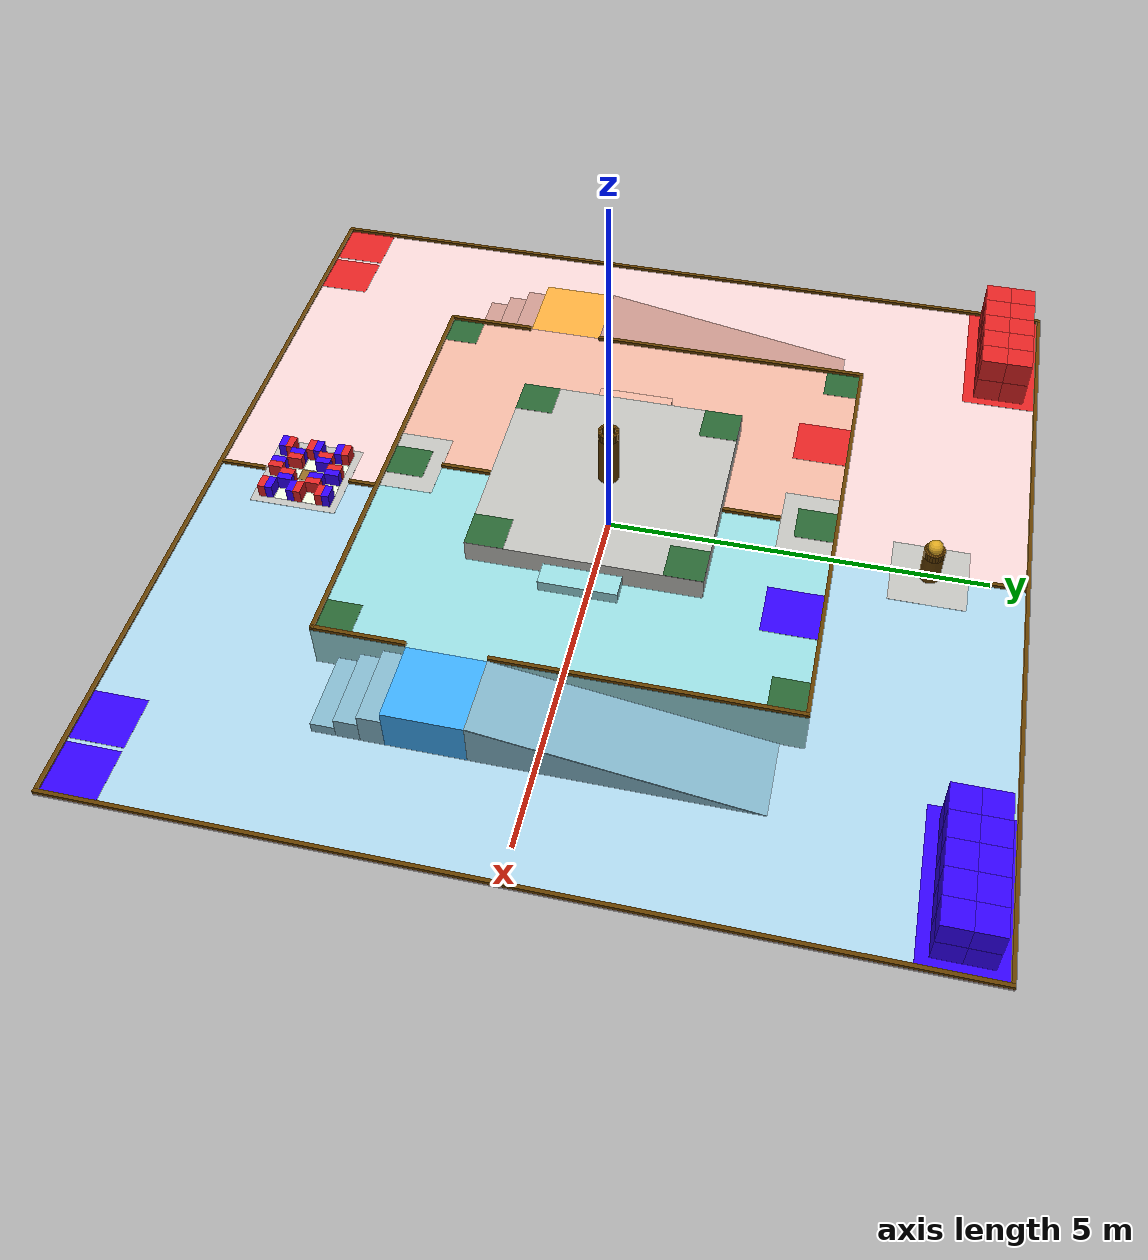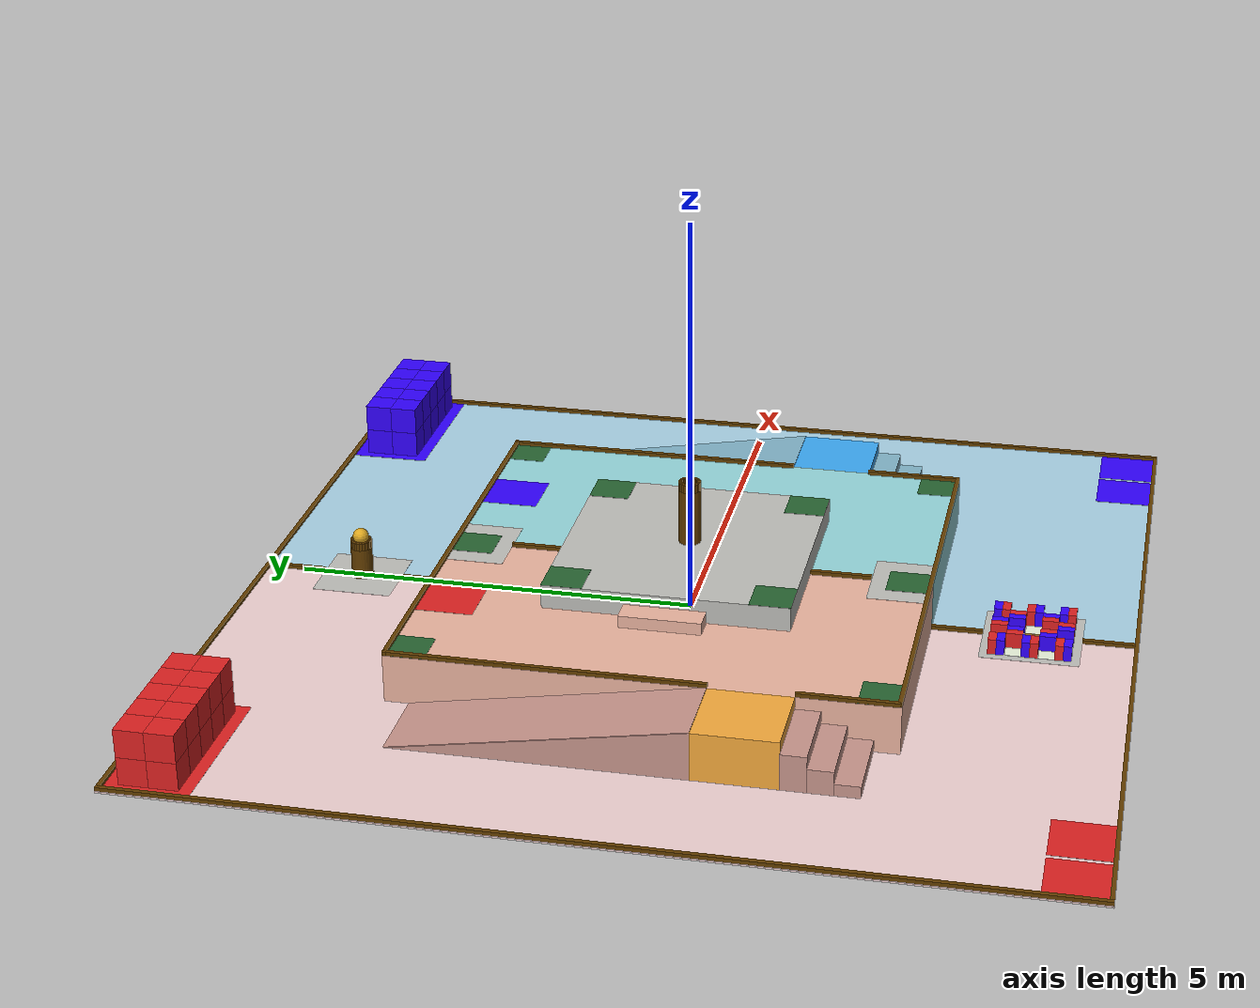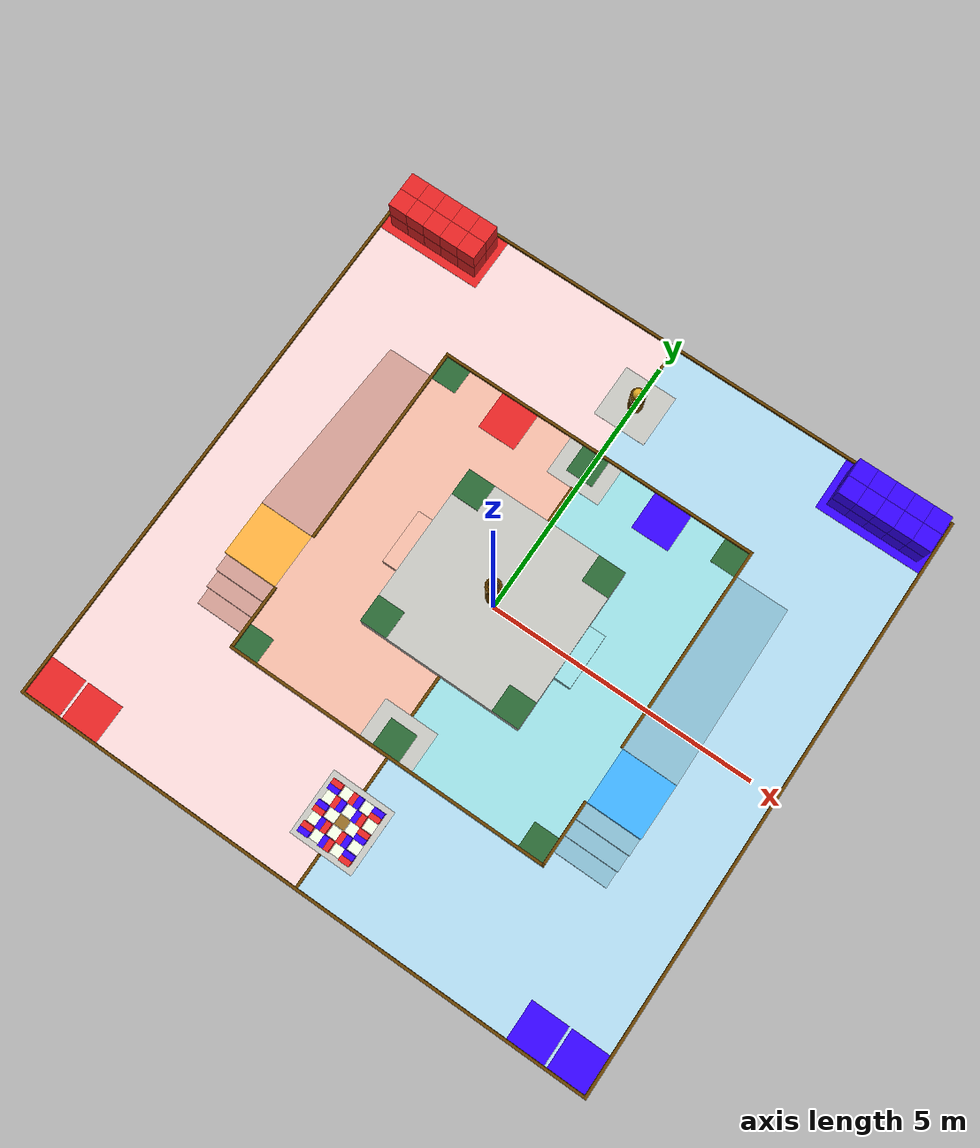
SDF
<?xml version='1.0' encoding='utf-8'?>
<sdf version="1.9">
  <world name="robocon_2027">
    <gravity>0 0 -9.8</gravity>
    <magnetic_field>0.000006 0.000023 -0.000042</magnetic_field>
    <scene>
      <ambient>0.62 0.62 0.62 1</ambient>
      <background>0.82 0.84 0.87 1</background>
      <shadows>true</shadows>
    </scene>
    <plugin name="gz::sim::systems::Physics" filename="gz-sim-physics-system" />
    <plugin name="gz::sim::systems::UserCommands" filename="gz-sim-user-commands-system" />
    <plugin name="gz::sim::systems::SceneBroadcaster" filename="gz-sim-scene-broadcaster-system" />
    <light name="sun" type="directional">
      <pose>0 0 10 0 0 0</pose>
      <diffuse>0.92 0.92 0.92 1</diffuse>
      <specular>0.2 0.2 0.2 1</specular>
      <direction>-0.35 0.25 -0.9</direction>
      <cast_shadows>true</cast_shadows>
    </light>
    <model name="robocon_2027_field">
      <static>true</static>
      <link name="ground_collision">
        <pose>0.000000 0.000000 -0.010000 0.000000 0.000000 0.000000</pose>
        <collision name="collision">
          <geometry>
            <box>
              <size>11.000000 11.000000 0.020000</size>
            </box>
          </geometry>
        </collision>
        <visual name="visual">
          <geometry>
            <box>
              <size>11.000000 11.000000 0.020000</size>
            </box>
          </geometry>
          <cast_shadows>true</cast_shadows>
          <material>
            <ambient>0.941176 0.823529 0.823529 1</ambient>
            <diffuse>0.941176 0.823529 0.823529 1</diffuse>
            <specular>0.08 0.08 0.08 1</specular>
            <double_sided>true</double_sided>
          </material>
        </visual>
      </link>
      <link name="ground_red">
        <pose>-2.750000 0.000000 0.001000 0.000000 0.000000 0.000000</pose>
        <visual name="visual">
          <geometry>
            <box>
              <size>5.500000 11.000000 0.002000</size>
            </box>
          </geometry>
          <cast_shadows>false</cast_shadows>
          <material>
            <ambient>0.941176 0.823529 0.823529 1</ambient>
            <diffuse>0.941176 0.823529 0.823529 1</diffuse>
            <specular>0.08 0.08 0.08 1</specular>
            <double_sided>true</double_sided>
          </material>
        </visual>
      </link>
      <link name="ground_blue">
        <pose>2.750000 0.000000 0.001000 0.000000 0.000000 0.000000</pose>
        <visual name="visual">
          <geometry>
            <box>
              <size>5.500000 11.000000 0.002000</size>
            </box>
          </geometry>
          <cast_shadows>false</cast_shadows>
          <material>
            <ambient>0.666667 0.823529 0.901961 1</ambient>
            <diffuse>0.666667 0.823529 0.901961 1</diffuse>
            <specular>0.08 0.08 0.08 1</specular>
            <double_sided>true</double_sided>
          </material>
        </visual>
      </link>
      <link name="storage_red">
        <pose>-4.450000 4.950000 0.003000 0.000000 0.000000 0.000000</pose>
        <visual name="visual">
          <geometry>
            <box>
              <size>2.000000 1.000000 0.002000</size>
            </box>
          </geometry>
          <cast_shadows>false</cast_shadows>
          <material>
            <ambient>0.874510 0.133333 0.133333 1</ambient>
            <diffuse>0.874510 0.133333 0.133333 1</diffuse>
            <specular>0.08 0.08 0.08 1</specular>
            <double_sided>true</double_sided>
          </material>
        </visual>
      </link>
      <link name="storage_blue">
        <pose>4.450000 4.950000 0.003000 0.000000 0.000000 0.000000</pose>
        <visual name="visual">
          <geometry>
            <box>
              <size>2.000000 1.000000 0.002000</size>
            </box>
          </geometry>
          <cast_shadows>false</cast_shadows>
          <material>
            <ambient>0.196078 0.000000 1.000000 1</ambient>
            <diffuse>0.196078 0.000000 1.000000 1</diffuse>
            <specular>0.08 0.08 0.08 1</specular>
            <double_sided>true</double_sided>
          </material>
        </visual>
      </link>
      <link name="start_red_outer">
        <pose>-5.100000 -5.100000 0.003000 0.000000 0.000000 0.000000</pose>
        <visual name="visual">
          <geometry>
            <box>
              <size>0.700000 0.700000 0.002000</size>
            </box>
          </geometry>
          <cast_shadows>false</cast_shadows>
          <material>
            <ambient>0.874510 0.133333 0.133333 1</ambient>
            <diffuse>0.874510 0.133333 0.133333 1</diffuse>
            <specular>0.08 0.08 0.08 1</specular>
            <double_sided>true</double_sided>
          </material>
        </visual>
      </link>
      <link name="start_red_inner">
        <pose>-4.350000 -5.100000 0.003000 0.000000 0.000000 0.000000</pose>
        <visual name="visual">
          <geometry>
            <box>
              <size>0.700000 0.700000 0.002000</size>
            </box>
          </geometry>
          <cast_shadows>false</cast_shadows>
          <material>
            <ambient>0.874510 0.133333 0.133333 1</ambient>
            <diffuse>0.874510 0.133333 0.133333 1</diffuse>
            <specular>0.08 0.08 0.08 1</specular>
            <double_sided>true</double_sided>
          </material>
        </visual>
      </link>
      <link name="start_blue_outer">
        <pose>5.100000 -5.100000 0.003000 0.000000 0.000000 0.000000</pose>
        <visual name="visual">
          <geometry>
            <box>
              <size>0.700000 0.700000 0.002000</size>
            </box>
          </geometry>
          <cast_shadows>false</cast_shadows>
          <material>
            <ambient>0.196078 0.000000 1.000000 1</ambient>
            <diffuse>0.196078 0.000000 1.000000 1</diffuse>
            <specular>0.08 0.08 0.08 1</specular>
            <double_sided>true</double_sided>
          </material>
        </visual>
      </link>
      <link name="start_blue_inner">
        <pose>4.350000 -5.100000 0.003000 0.000000 0.000000 0.000000</pose>
        <visual name="visual">
          <geometry>
            <box>
              <size>0.700000 0.700000 0.002000</size>
            </box>
          </geometry>
          <cast_shadows>false</cast_shadows>
          <material>
            <ambient>0.196078 0.000000 1.000000 1</ambient>
            <diffuse>0.196078 0.000000 1.000000 1</diffuse>
            <specular>0.08 0.08 0.08 1</specular>
            <double_sided>true</double_sided>
          </material>
        </visual>
      </link>
      <link name="mustika_shared_ground">
        <pose>0.000000 4.225000 0.003000 0.000000 0.000000 0.000000</pose>
        <visual name="visual">
          <geometry>
            <box>
              <size>1.000000 1.000000 0.002000</size>
            </box>
          </geometry>
          <cast_shadows>false</cast_shadows>
          <material>
            <ambient>0.745098 0.745098 0.725490 1</ambient>
            <diffuse>0.745098 0.745098 0.725490 1</diffuse>
            <specular>0.08 0.08 0.08 1</specular>
            <double_sided>true</double_sided>
          </material>
        </visual>
      </link>
      <link name="sky_shared_ground">
        <pose>0.000000 -4.225000 0.003000 0.000000 0.000000 0.000000</pose>
        <visual name="visual">
          <geometry>
            <box>
              <size>1.200000 1.200000 0.002000</size>
            </box>
          </geometry>
          <cast_shadows>false</cast_shadows>
          <material>
            <ambient>0.745098 0.745098 0.725490 1</ambient>
            <diffuse>0.745098 0.745098 0.725490 1</diffuse>
            <specular>0.08 0.08 0.08 1</specular>
            <double_sided>true</double_sided>
          </material>
        </visual>
      </link>
      <link name="sky_grid_0_0">
        <pose>-0.400000 -4.625000 0.006000 0.000000 0.000000 0.000000</pose>
        <visual name="visual">
          <geometry>
            <box>
              <size>0.192000 0.192000 0.002000</size>
            </box>
          </geometry>
          <cast_shadows>false</cast_shadows>
          <material>
            <ambient>0.803922 0.901961 0.745098 1</ambient>
            <diffuse>0.803922 0.901961 0.745098 1</diffuse>
            <specular>0.08 0.08 0.08 1</specular>
            <double_sided>true</double_sided>
          </material>
        </visual>
      </link>
      <link name="sky_grid_0_1">
        <pose>-0.200000 -4.625000 0.006000 0.000000 0.000000 0.000000</pose>
        <visual name="visual">
          <geometry>
            <box>
              <size>0.192000 0.192000 0.002000</size>
            </box>
          </geometry>
          <cast_shadows>false</cast_shadows>
          <material>
            <ambient>0.921569 0.960784 0.862745 1</ambient>
            <diffuse>0.921569 0.960784 0.862745 1</diffuse>
            <specular>0.08 0.08 0.08 1</specular>
            <double_sided>true</double_sided>
          </material>
        </visual>
      </link>
      <link name="sky_grid_0_2">
        <pose>0.000000 -4.625000 0.006000 0.000000 0.000000 0.000000</pose>
        <visual name="visual">
          <geometry>
            <box>
              <size>0.192000 0.192000 0.002000</size>
            </box>
          </geometry>
          <cast_shadows>false</cast_shadows>
          <material>
            <ambient>0.803922 0.901961 0.745098 1</ambient>
            <diffuse>0.803922 0.901961 0.745098 1</diffuse>
            <specular>0.08 0.08 0.08 1</specular>
            <double_sided>true</double_sided>
          </material>
        </visual>
      </link>
      <link name="sky_grid_0_3">
        <pose>0.200000 -4.625000 0.006000 0.000000 0.000000 0.000000</pose>
        <visual name="visual">
          <geometry>
            <box>
              <size>0.192000 0.192000 0.002000</size>
            </box>
          </geometry>
          <cast_shadows>false</cast_shadows>
          <material>
            <ambient>0.921569 0.960784 0.862745 1</ambient>
            <diffuse>0.921569 0.960784 0.862745 1</diffuse>
            <specular>0.08 0.08 0.08 1</specular>
            <double_sided>true</double_sided>
          </material>
        </visual>
      </link>
      <link name="sky_grid_0_4">
        <pose>0.400000 -4.625000 0.006000 0.000000 0.000000 0.000000</pose>
        <visual name="visual">
          <geometry>
            <box>
              <size>0.192000 0.192000 0.002000</size>
            </box>
          </geometry>
          <cast_shadows>false</cast_shadows>
          <material>
            <ambient>0.803922 0.901961 0.745098 1</ambient>
            <diffuse>0.803922 0.901961 0.745098 1</diffuse>
            <specular>0.08 0.08 0.08 1</specular>
            <double_sided>true</double_sided>
          </material>
        </visual>
      </link>
      <link name="sky_grid_1_0">
        <pose>-0.400000 -4.425000 0.006000 0.000000 0.000000 0.000000</pose>
        <visual name="visual">
          <geometry>
            <box>
              <size>0.192000 0.192000 0.002000</size>
            </box>
          </geometry>
          <cast_shadows>false</cast_shadows>
          <material>
            <ambient>0.921569 0.960784 0.862745 1</ambient>
            <diffuse>0.921569 0.960784 0.862745 1</diffuse>
            <specular>0.08 0.08 0.08 1</specular>
            <double_sided>true</double_sided>
          </material>
        </visual>
      </link>
      <link name="sky_grid_1_1">
        <pose>-0.200000 -4.425000 0.006000 0.000000 0.000000 0.000000</pose>
        <visual name="visual">
          <geometry>
            <box>
              <size>0.192000 0.192000 0.002000</size>
            </box>
          </geometry>
          <cast_shadows>false</cast_shadows>
          <material>
            <ambient>0.803922 0.901961 0.745098 1</ambient>
            <diffuse>0.803922 0.901961 0.745098 1</diffuse>
            <specular>0.08 0.08 0.08 1</specular>
            <double_sided>true</double_sided>
          </material>
        </visual>
      </link>
      <link name="sky_grid_1_2">
        <pose>0.000000 -4.425000 0.006000 0.000000 0.000000 0.000000</pose>
        <visual name="visual">
          <geometry>
            <box>
              <size>0.192000 0.192000 0.002000</size>
            </box>
          </geometry>
          <cast_shadows>false</cast_shadows>
          <material>
            <ambient>0.921569 0.960784 0.862745 1</ambient>
            <diffuse>0.921569 0.960784 0.862745 1</diffuse>
            <specular>0.08 0.08 0.08 1</specular>
            <double_sided>true</double_sided>
          </material>
        </visual>
      </link>
      <link name="sky_grid_1_3">
        <pose>0.200000 -4.425000 0.006000 0.000000 0.000000 0.000000</pose>
        <visual name="visual">
          <geometry>
            <box>
              <size>0.192000 0.192000 0.002000</size>
            </box>
          </geometry>
          <cast_shadows>false</cast_shadows>
          <material>
            <ambient>0.803922 0.901961 0.745098 1</ambient>
            <diffuse>0.803922 0.901961 0.745098 1</diffuse>
            <specular>0.08 0.08 0.08 1</specular>
            <double_sided>true</double_sided>
          </material>
        </visual>
      </link>
      <link name="sky_grid_1_4">
        <pose>0.400000 -4.425000 0.006000 0.000000 0.000000 0.000000</pose>
        <visual name="visual">
          <geometry>
            <box>
              <size>0.192000 0.192000 0.002000</size>
            </box>
          </geometry>
          <cast_shadows>false</cast_shadows>
          <material>
            <ambient>0.921569 0.960784 0.862745 1</ambient>
            <diffuse>0.921569 0.960784 0.862745 1</diffuse>
            <specular>0.08 0.08 0.08 1</specular>
            <double_sided>true</double_sided>
          </material>
        </visual>
      </link>
      <link name="sky_grid_2_0">
        <pose>-0.400000 -4.225000 0.006000 0.000000 0.000000 0.000000</pose>
        <visual name="visual">
          <geometry>
            <box>
              <size>0.192000 0.192000 0.002000</size>
            </box>
          </geometry>
          <cast_shadows>false</cast_shadows>
          <material>
            <ambient>0.803922 0.901961 0.745098 1</ambient>
            <diffuse>0.803922 0.901961 0.745098 1</diffuse>
            <specular>0.08 0.08 0.08 1</specular>
            <double_sided>true</double_sided>
          </material>
        </visual>
      </link>
      <link name="sky_grid_2_1">
        <pose>-0.200000 -4.225000 0.006000 0.000000 0.000000 0.000000</pose>
        <visual name="visual">
          <geometry>
            <box>
              <size>0.192000 0.192000 0.002000</size>
            </box>
          </geometry>
          <cast_shadows>false</cast_shadows>
          <material>
            <ambient>0.921569 0.960784 0.862745 1</ambient>
            <diffuse>0.921569 0.960784 0.862745 1</diffuse>
            <specular>0.08 0.08 0.08 1</specular>
            <double_sided>true</double_sided>
          </material>
        </visual>
      </link>
      <link name="sky_grid_2_2">
        <pose>0.000000 -4.225000 0.006000 0.000000 0.000000 0.000000</pose>
        <visual name="visual">
          <geometry>
            <box>
              <size>0.192000 0.192000 0.002000</size>
            </box>
          </geometry>
          <cast_shadows>false</cast_shadows>
          <material>
            <ambient>0.568627 0.411765 0.137255 1</ambient>
            <diffuse>0.568627 0.411765 0.137255 1</diffuse>
            <specular>0.08 0.08 0.08 1</specular>
            <double_sided>true</double_sided>
          </material>
        </visual>
      </link>
      <link name="sky_grid_2_3">
        <pose>0.200000 -4.225000 0.006000 0.000000 0.000000 0.000000</pose>
        <visual name="visual">
          <geometry>
            <box>
              <size>0.192000 0.192000 0.002000</size>
            </box>
          </geometry>
          <cast_shadows>false</cast_shadows>
          <material>
            <ambient>0.921569 0.960784 0.862745 1</ambient>
            <diffuse>0.921569 0.960784 0.862745 1</diffuse>
            <specular>0.08 0.08 0.08 1</specular>
            <double_sided>true</double_sided>
          </material>
        </visual>
      </link>
      <link name="sky_grid_2_4">
        <pose>0.400000 -4.225000 0.006000 0.000000 0.000000 0.000000</pose>
        <visual name="visual">
          <geometry>
            <box>
              <size>0.192000 0.192000 0.002000</size>
            </box>
          </geometry>
          <cast_shadows>false</cast_shadows>
          <material>
            <ambient>0.803922 0.901961 0.745098 1</ambient>
            <diffuse>0.803922 0.901961 0.745098 1</diffuse>
            <specular>0.08 0.08 0.08 1</specular>
            <double_sided>true</double_sided>
          </material>
        </visual>
      </link>
      <link name="sky_grid_3_0">
        <pose>-0.400000 -4.025000 0.006000 0.000000 0.000000 0.000000</pose>
        <visual name="visual">
          <geometry>
            <box>
              <size>0.192000 0.192000 0.002000</size>
            </box>
          </geometry>
          <cast_shadows>false</cast_shadows>
          <material>
            <ambient>0.921569 0.960784 0.862745 1</ambient>
            <diffuse>0.921569 0.960784 0.862745 1</diffuse>
            <specular>0.08 0.08 0.08 1</specular>
            <double_sided>true</double_sided>
          </material>
        </visual>
      </link>
      <link name="sky_grid_3_1">
        <pose>-0.200000 -4.025000 0.006000 0.000000 0.000000 0.000000</pose>
        <visual name="visual">
          <geometry>
            <box>
              <size>0.192000 0.192000 0.002000</size>
            </box>
          </geometry>
          <cast_shadows>false</cast_shadows>
          <material>
            <ambient>0.803922 0.901961 0.745098 1</ambient>
            <diffuse>0.803922 0.901961 0.745098 1</diffuse>
            <specular>0.08 0.08 0.08 1</specular>
            <double_sided>true</double_sided>
          </material>
        </visual>
      </link>
      <link name="sky_grid_3_2">
        <pose>0.000000 -4.025000 0.006000 0.000000 0.000000 0.000000</pose>
        <visual name="visual">
          <geometry>
            <box>
              <size>0.192000 0.192000 0.002000</size>
            </box>
          </geometry>
          <cast_shadows>false</cast_shadows>
          <material>
            <ambient>0.921569 0.960784 0.862745 1</ambient>
            <diffuse>0.921569 0.960784 0.862745 1</diffuse>
            <specular>0.08 0.08 0.08 1</specular>
            <double_sided>true</double_sided>
          </material>
        </visual>
      </link>
      <link name="sky_grid_3_3">
        <pose>0.200000 -4.025000 0.006000 0.000000 0.000000 0.000000</pose>
        <visual name="visual">
          <geometry>
            <box>
              <size>0.192000 0.192000 0.002000</size>
            </box>
          </geometry>
          <cast_shadows>false</cast_shadows>
          <material>
            <ambient>0.803922 0.901961 0.745098 1</ambient>
            <diffuse>0.803922 0.901961 0.745098 1</diffuse>
            <specular>0.08 0.08 0.08 1</specular>
            <double_sided>true</double_sided>
          </material>
        </visual>
      </link>
      <link name="sky_grid_3_4">
        <pose>0.400000 -4.025000 0.006000 0.000000 0.000000 0.000000</pose>
        <visual name="visual">
          <geometry>
            <box>
              <size>0.192000 0.192000 0.002000</size>
            </box>
          </geometry>
          <cast_shadows>false</cast_shadows>
          <material>
            <ambient>0.921569 0.960784 0.862745 1</ambient>
            <diffuse>0.921569 0.960784 0.862745 1</diffuse>
            <specular>0.08 0.08 0.08 1</specular>
            <double_sided>true</double_sided>
          </material>
        </visual>
      </link>
      <link name="sky_grid_4_0">
        <pose>-0.400000 -3.825000 0.006000 0.000000 0.000000 0.000000</pose>
        <visual name="visual">
          <geometry>
            <box>
              <size>0.192000 0.192000 0.002000</size>
            </box>
          </geometry>
          <cast_shadows>false</cast_shadows>
          <material>
            <ambient>0.803922 0.901961 0.745098 1</ambient>
            <diffuse>0.803922 0.901961 0.745098 1</diffuse>
            <specular>0.08 0.08 0.08 1</specular>
            <double_sided>true</double_sided>
          </material>
        </visual>
      </link>
      <link name="sky_grid_4_1">
        <pose>-0.200000 -3.825000 0.006000 0.000000 0.000000 0.000000</pose>
        <visual name="visual">
          <geometry>
            <box>
              <size>0.192000 0.192000 0.002000</size>
            </box>
          </geometry>
          <cast_shadows>false</cast_shadows>
          <material>
            <ambient>0.921569 0.960784 0.862745 1</ambient>
            <diffuse>0.921569 0.960784 0.862745 1</diffuse>
            <specular>0.08 0.08 0.08 1</specular>
            <double_sided>true</double_sided>
          </material>
        </visual>
      </link>
      <link name="sky_grid_4_2">
        <pose>0.000000 -3.825000 0.006000 0.000000 0.000000 0.000000</pose>
        <visual name="visual">
          <geometry>
            <box>
              <size>0.192000 0.192000 0.002000</size>
            </box>
          </geometry>
          <cast_shadows>false</cast_shadows>
          <material>
            <ambient>0.803922 0.901961 0.745098 1</ambient>
            <diffuse>0.803922 0.901961 0.745098 1</diffuse>
            <specular>0.08 0.08 0.08 1</specular>
            <double_sided>true</double_sided>
          </material>
        </visual>
      </link>
      <link name="sky_grid_4_3">
        <pose>0.200000 -3.825000 0.006000 0.000000 0.000000 0.000000</pose>
        <visual name="visual">
          <geometry>
            <box>
              <size>0.192000 0.192000 0.002000</size>
            </box>
          </geometry>
          <cast_shadows>false</cast_shadows>
          <material>
            <ambient>0.921569 0.960784 0.862745 1</ambient>
            <diffuse>0.921569 0.960784 0.862745 1</diffuse>
            <specular>0.08 0.08 0.08 1</specular>
            <double_sided>true</double_sided>
          </material>
        </visual>
      </link>
      <link name="sky_grid_4_4">
        <pose>0.400000 -3.825000 0.006000 0.000000 0.000000 0.000000</pose>
        <visual name="visual">
          <geometry>
            <box>
              <size>0.192000 0.192000 0.002000</size>
            </box>
          </geometry>
          <cast_shadows>false</cast_shadows>
          <material>
            <ambient>0.803922 0.901961 0.745098 1</ambient>
            <diffuse>0.803922 0.901961 0.745098 1</diffuse>
            <specular>0.08 0.08 0.08 1</specular>
            <double_sided>true</double_sided>
          </material>
        </visual>
      </link>
      <link name="wall_ground_x_pos">
        <pose>5.475000 0.000000 0.025000 0.000000 0.000000 0.000000</pose>
        <collision name="collision">
          <geometry>
            <box>
              <size>0.050000 11.000000 0.050000</size>
            </box>
          </geometry>
        </collision>
        <visual name="visual">
          <geometry>
            <box>
              <size>0.050000 11.000000 0.050000</size>
            </box>
          </geometry>
          <cast_shadows>true</cast_shadows>
          <material>
            <ambient>0.392157 0.243137 0.000000 1</ambient>
            <diffuse>0.392157 0.243137 0.000000 1</diffuse>
            <specular>0.08 0.08 0.08 1</specular>
            <double_sided>true</double_sided>
          </material>
        </visual>
      </link>
      <link name="wall_ground_x_neg">
        <pose>-5.475000 0.000000 0.025000 0.000000 0.000000 0.000000</pose>
        <collision name="collision">
          <geometry>
            <box>
              <size>0.050000 11.000000 0.050000</size>
            </box>
          </geometry>
        </collision>
        <visual name="visual">
          <geometry>
            <box>
              <size>0.050000 11.000000 0.050000</size>
            </box>
          </geometry>
          <cast_shadows>true</cast_shadows>
          <material>
            <ambient>0.392157 0.243137 0.000000 1</ambient>
            <diffuse>0.392157 0.243137 0.000000 1</diffuse>
            <specular>0.08 0.08 0.08 1</specular>
            <double_sided>true</double_sided>
          </material>
        </visual>
      </link>
      <link name="wall_ground_y_pos">
        <pose>0.000000 5.475000 0.025000 0.000000 0.000000 0.000000</pose>
        <collision name="collision">
          <geometry>
            <box>
              <size>10.900000 0.050000 0.050000</size>
            </box>
          </geometry>
        </collision>
        <visual name="visual">
          <geometry>
            <box>
              <size>10.900000 0.050000 0.050000</size>
            </box>
          </geometry>
          <cast_shadows>true</cast_shadows>
          <material>
            <ambient>0.392157 0.243137 0.000000 1</ambient>
            <diffuse>0.392157 0.243137 0.000000 1</diffuse>
            <specular>0.08 0.08 0.08 1</specular>
            <double_sided>true</double_sided>
          </material>
        </visual>
      </link>
      <link name="wall_ground_y_neg">
        <pose>0.000000 -5.475000 0.025000 0.000000 0.000000 0.000000</pose>
        <collision name="collision">
          <geometry>
            <box>
              <size>10.900000 0.050000 0.050000</size>
            </box>
          </geometry>
        </collision>
        <visual name="visual">
          <geometry>
            <box>
              <size>10.900000 0.050000 0.050000</size>
            </box>
          </geometry>
          <cast_shadows>true</cast_shadows>
          <material>
            <ambient>0.392157 0.243137 0.000000 1</ambient>
            <diffuse>0.392157 0.243137 0.000000 1</diffuse>
            <specular>0.08 0.08 0.08 1</specular>
            <double_sided>true</double_sided>
          </material>
        </visual>
      </link>
      <link name="wall_ground_divider_positive_inner">
        <pose>0.000000 3.362500 0.025000 0.000000 0.000000 0.000000</pose>
        <collision name="collision">
          <geometry>
            <box>
              <size>0.050000 0.725000 0.050000</size>
            </box>
          </geometry>
        </collision>
        <visual name="visual">
          <geometry>
            <box>
              <size>0.050000 0.725000 0.050000</size>
            </box>
          </geometry>
          <cast_shadows>true</cast_shadows>
          <material>
            <ambient>0.392157 0.243137 0.000000 1</ambient>
            <diffuse>0.392157 0.243137 0.000000 1</diffuse>
            <specular>0.08 0.08 0.08 1</specular>
            <double_sided>true</double_sided>
          </material>
        </visual>
      </link>
      <link name="wall_ground_divider_positive_outer">
        <pose>0.000000 5.087500 0.025000 0.000000 0.000000 0.000000</pose>
        <collision name="collision">
          <geometry>
            <box>
              <size>0.050000 0.725000 0.050000</size>
            </box>
          </geometry>
        </collision>
        <visual name="visual">
          <geometry>
            <box>
              <size>0.050000 0.725000 0.050000</size>
            </box>
          </geometry>
          <cast_shadows>true</cast_shadows>
          <material>
            <ambient>0.392157 0.243137 0.000000 1</ambient>
            <diffuse>0.392157 0.243137 0.000000 1</diffuse>
            <specular>0.08 0.08 0.08 1</specular>
            <double_sided>true</double_sided>
          </material>
        </visual>
      </link>
      <link name="wall_ground_divider_negative_inner">
        <pose>0.000000 -3.312500 0.025000 0.000000 0.000000 0.000000</pose>
        <collision name="collision">
          <geometry>
            <box>
              <size>0.050000 0.625000 0.050000</size>
            </box>
          </geometry>
        </collision>
        <visual name="visual">
          <geometry>
            <box>
              <size>0.050000 0.625000 0.050000</size>
            </box>
          </geometry>
          <cast_shadows>true</cast_shadows>
          <material>
            <ambient>0.392157 0.243137 0.000000 1</ambient>
            <diffuse>0.392157 0.243137 0.000000 1</diffuse>
            <specular>0.08 0.08 0.08 1</specular>
            <double_sided>true</double_sided>
          </material>
        </visual>
      </link>
      <link name="wall_ground_divider_negative_outer">
        <pose>0.000000 -5.137500 0.025000 0.000000 0.000000 0.000000</pose>
        <collision name="collision">
          <geometry>
            <box>
              <size>0.050000 0.625000 0.050000</size>
            </box>
          </geometry>
        </collision>
        <visual name="visual">
          <geometry>
            <box>
              <size>0.050000 0.625000 0.050000</size>
            </box>
          </geometry>
          <cast_shadows>true</cast_shadows>
          <material>
            <ambient>0.392157 0.243137 0.000000 1</ambient>
            <diffuse>0.392157 0.243137 0.000000 1</diffuse>
            <specular>0.08 0.08 0.08 1</specular>
            <double_sided>true</double_sided>
          </material>
        </visual>
      </link>
      <link name="l1_red">
        <pose>-1.500000 0.000000 0.300000 0.000000 0.000000 0.000000</pose>
        <collision name="collision">
          <geometry>
            <box>
              <size>3.000000 6.000000 0.600000</size>
            </box>
          </geometry>
        </collision>
        <visual name="visual">
          <geometry>
            <box>
              <size>3.000000 6.000000 0.600000</size>
            </box>
          </geometry>
          <cast_shadows>true</cast_shadows>
          <material>
            <ambient>0.921569 0.705882 0.627451 1</ambient>
            <diffuse>0.921569 0.705882 0.627451 1</diffuse>
            <specular>0.08 0.08 0.08 1</specular>
            <double_sided>true</double_sided>
          </material>
        </visual>
      </link>
      <link name="l1_blue">
        <pose>1.500000 0.000000 0.300000 0.000000 0.000000 0.000000</pose>
        <collision name="collision">
          <geometry>
            <box>
              <size>3.000000 6.000000 0.600000</size>
            </box>
          </geometry>
        </collision>
        <visual name="visual">
          <geometry>
            <box>
              <size>3.000000 6.000000 0.600000</size>
            </box>
          </geometry>
          <cast_shadows>true</cast_shadows>
          <material>
            <ambient>0.588235 0.843137 0.862745 1</ambient>
            <diffuse>0.588235 0.843137 0.862745 1</diffuse>
            <specular>0.08 0.08 0.08 1</specular>
            <double_sided>true</double_sided>
          </material>
        </visual>
      </link>
      <link name="l1_shared_positive">
        <pose>0.000000 2.625000 0.601000 0.000000 0.000000 0.000000</pose>
        <visual name="visual">
          <geometry>
            <box>
              <size>1.000000 0.750000 0.002000</size>
            </box>
          </geometry>
          <cast_shadows>false</cast_shadows>
          <material>
            <ambient>0.745098 0.745098 0.725490 1</ambient>
            <diffuse>0.745098 0.745098 0.725490 1</diffuse>
            <specular>0.08 0.08 0.08 1</specular>
            <double_sided>true</double_sided>
          </material>
        </visual>
      </link>
      <link name="l1_shared_spot_positive">
        <pose>0.000000 2.700000 0.603000 0.000000 0.000000 0.000000</pose>
        <visual name="visual">
          <geometry>
            <box>
              <size>0.500000 0.500000 0.002000</size>
            </box>
          </geometry>
          <cast_shadows>false</cast_shadows>
          <material>
            <ambient>0.156863 0.392157 0.196078 1</ambient>
            <diffuse>0.156863 0.392157 0.196078 1</diffuse>
            <specular>0.08 0.08 0.08 1</specular>
            <double_sided>true</double_sided>
          </material>
        </visual>
      </link>
      <link name="l1_shared_negative">
        <pose>0.000000 -2.625000 0.601000 0.000000 0.000000 0.000000</pose>
        <visual name="visual">
          <geometry>
            <box>
              <size>1.000000 0.750000 0.002000</size>
            </box>
          </geometry>
          <cast_shadows>false</cast_shadows>
          <material>
            <ambient>0.745098 0.745098 0.725490 1</ambient>
            <diffuse>0.745098 0.745098 0.725490 1</diffuse>
            <specular>0.08 0.08 0.08 1</specular>
            <double_sided>true</double_sided>
          </material>
        </visual>
      </link>
      <link name="l1_shared_spot_negative">
        <pose>0.000000 -2.700000 0.603000 0.000000 0.000000 0.000000</pose>
        <visual name="visual">
          <geometry>
            <box>
              <size>0.500000 0.500000 0.002000</size>
            </box>
          </geometry>
          <cast_shadows>false</cast_shadows>
          <material>
            <ambient>0.156863 0.392157 0.196078 1</ambient>
            <diffuse>0.156863 0.392157 0.196078 1</diffuse>
            <specular>0.08 0.08 0.08 1</specular>
            <double_sided>true</double_sided>
          </material>
        </visual>
      </link>
      <link name="l1_spot_red_positive">
        <pose>-2.750000 2.750000 0.603000 0.000000 0.000000 0.000000</pose>
        <visual name="visual">
          <geometry>
            <box>
              <size>0.500000 0.500000 0.002000</size>
            </box>
          </geometry>
          <cast_shadows>false</cast_shadows>
          <material>
            <ambient>0.156863 0.392157 0.196078 1</ambient>
            <diffuse>0.156863 0.392157 0.196078 1</diffuse>
            <specular>0.08 0.08 0.08 1</specular>
            <double_sided>true</double_sided>
          </material>
        </visual>
      </link>
      <link name="l1_spot_red_negative">
        <pose>-2.750000 -2.750000 0.603000 0.000000 0.000000 0.000000</pose>
        <visual name="visual">
          <geometry>
            <box>
              <size>0.500000 0.500000 0.002000</size>
            </box>
          </geometry>
          <cast_shadows>false</cast_shadows>
          <material>
            <ambient>0.156863 0.392157 0.196078 1</ambient>
            <diffuse>0.156863 0.392157 0.196078 1</diffuse>
            <specular>0.08 0.08 0.08 1</specular>
            <double_sided>true</double_sided>
          </material>
        </visual>
      </link>
      <link name="l1_retry_red">
        <pose>-1.500000 2.600000 0.603000 0.000000 0.000000 0.000000</pose>
        <visual name="visual">
          <geometry>
            <box>
              <size>0.700000 0.700000 0.002000</size>
            </box>
          </geometry>
          <cast_shadows>false</cast_shadows>
          <material>
            <ambient>0.874510 0.133333 0.133333 1</ambient>
            <diffuse>0.874510 0.133333 0.133333 1</diffuse>
            <specular>0.08 0.08 0.08 1</specular>
            <double_sided>true</double_sided>
          </material>
        </visual>
      </link>
      <link name="l1_spot_blue_positive">
        <pose>2.750000 2.750000 0.603000 0.000000 0.000000 0.000000</pose>
        <visual name="visual">
          <geometry>
            <box>
              <size>0.500000 0.500000 0.002000</size>
            </box>
          </geometry>
          <cast_shadows>false</cast_shadows>
          <material>
            <ambient>0.156863 0.392157 0.196078 1</ambient>
            <diffuse>0.156863 0.392157 0.196078 1</diffuse>
            <specular>0.08 0.08 0.08 1</specular>
            <double_sided>true</double_sided>
          </material>
        </visual>
      </link>
      <link name="l1_spot_blue_negative">
        <pose>2.750000 -2.750000 0.603000 0.000000 0.000000 0.000000</pose>
        <visual name="visual">
          <geometry>
            <box>
              <size>0.500000 0.500000 0.002000</size>
            </box>
          </geometry>
          <cast_shadows>false</cast_shadows>
          <material>
            <ambient>0.156863 0.392157 0.196078 1</ambient>
            <diffuse>0.156863 0.392157 0.196078 1</diffuse>
            <specular>0.08 0.08 0.08 1</specular>
            <double_sided>true</double_sided>
          </material>
        </visual>
      </link>
      <link name="l1_retry_blue">
        <pose>1.500000 2.600000 0.603000 0.000000 0.000000 0.000000</pose>
        <visual name="visual">
          <geometry>
            <box>
              <size>0.700000 0.700000 0.002000</size>
            </box>
          </geometry>
          <cast_shadows>false</cast_shadows>
          <material>
            <ambient>0.196078 0.000000 1.000000 1</ambient>
            <diffuse>0.196078 0.000000 1.000000 1</diffuse>
            <specular>0.08 0.08 0.08 1</specular>
            <double_sided>true</double_sided>
          </material>
        </visual>
      </link>
      <link name="wall_l1_y_pos">
        <pose>0.000000 2.975000 0.625000 0.000000 0.000000 0.000000</pose>
        <collision name="collision">
          <geometry>
            <box>
              <size>6.000000 0.050000 0.050000</size>
            </box>
          </geometry>
        </collision>
        <visual name="visual">
          <geometry>
            <box>
              <size>6.000000 0.050000 0.050000</size>
            </box>
          </geometry>
          <cast_shadows>true</cast_shadows>
          <material>
            <ambient>0.392157 0.243137 0.000000 1</ambient>
            <diffuse>0.392157 0.243137 0.000000 1</diffuse>
            <specular>0.08 0.08 0.08 1</specular>
            <double_sided>true</double_sided>
          </material>
        </visual>
      </link>
      <link name="wall_l1_y_neg">
        <pose>0.000000 -2.975000 0.625000 0.000000 0.000000 0.000000</pose>
        <collision name="collision">
          <geometry>
            <box>
              <size>6.000000 0.050000 0.050000</size>
            </box>
          </geometry>
        </collision>
        <visual name="visual">
          <geometry>
            <box>
              <size>6.000000 0.050000 0.050000</size>
            </box>
          </geometry>
          <cast_shadows>true</cast_shadows>
          <material>
            <ambient>0.392157 0.243137 0.000000 1</ambient>
            <diffuse>0.392157 0.243137 0.000000 1</diffuse>
            <specular>0.08 0.08 0.08 1</specular>
            <double_sided>true</double_sided>
          </material>
        </visual>
      </link>
      <link name="wall_l1_red_before_transfer">
        <pose>-2.975000 -2.400000 0.625000 0.000000 0.000000 0.000000</pose>
        <collision name="collision">
          <geometry>
            <box>
              <size>0.050000 1.200000 0.050000</size>
            </box>
          </geometry>
        </collision>
        <visual name="visual">
          <geometry>
            <box>
              <size>0.050000 1.200000 0.050000</size>
            </box>
          </geometry>
          <cast_shadows>true</cast_shadows>
          <material>
            <ambient>0.392157 0.243137 0.000000 1</ambient>
            <diffuse>0.392157 0.243137 0.000000 1</diffuse>
            <specular>0.08 0.08 0.08 1</specular>
            <double_sided>true</double_sided>
          </material>
        </visual>
      </link>
      <link name="wall_l1_red_after_transfer">
        <pose>-2.975000 1.100000 0.625000 0.000000 0.000000 0.000000</pose>
        <collision name="collision">
          <geometry>
            <box>
              <size>0.050000 3.800000 0.050000</size>
            </box>
          </geometry>
        </collision>
        <visual name="visual">
          <geometry>
            <box>
              <size>0.050000 3.800000 0.050000</size>
            </box>
          </geometry>
          <cast_shadows>true</cast_shadows>
          <material>
            <ambient>0.392157 0.243137 0.000000 1</ambient>
            <diffuse>0.392157 0.243137 0.000000 1</diffuse>
            <specular>0.08 0.08 0.08 1</specular>
            <double_sided>true</double_sided>
          </material>
        </visual>
      </link>
      <link name="wall_l1_blue_before_transfer">
        <pose>2.975000 -2.400000 0.625000 0.000000 0.000000 0.000000</pose>
        <collision name="collision">
          <geometry>
            <box>
              <size>0.050000 1.200000 0.050000</size>
            </box>
          </geometry>
        </collision>
        <visual name="visual">
          <geometry>
            <box>
              <size>0.050000 1.200000 0.050000</size>
            </box>
          </geometry>
          <cast_shadows>true</cast_shadows>
          <material>
            <ambient>0.392157 0.243137 0.000000 1</ambient>
            <diffuse>0.392157 0.243137 0.000000 1</diffuse>
            <specular>0.08 0.08 0.08 1</specular>
            <double_sided>true</double_sided>
          </material>
        </visual>
      </link>
      <link name="wall_l1_blue_after_transfer">
        <pose>2.975000 1.100000 0.625000 0.000000 0.000000 0.000000</pose>
        <collision name="collision">
          <geometry>
            <box>
              <size>0.050000 3.800000 0.050000</size>
            </box>
          </geometry>
        </collision>
        <visual name="visual">
          <geometry>
            <box>
              <size>0.050000 3.800000 0.050000</size>
            </box>
          </geometry>
          <cast_shadows>true</cast_shadows>
          <material>
            <ambient>0.392157 0.243137 0.000000 1</ambient>
            <diffuse>0.392157 0.243137 0.000000 1</diffuse>
            <specular>0.08 0.08 0.08 1</specular>
            <double_sided>true</double_sided>
          </material>
        </visual>
      </link>
      <link name="wall_l1_divider_positive">
        <pose>0.000000 1.875000 0.625000 0.000000 0.000000 0.000000</pose>
        <collision name="collision">
          <geometry>
            <box>
              <size>0.050000 0.750000 0.050000</size>
            </box>
          </geometry>
        </collision>
        <visual name="visual">
          <geometry>
            <box>
              <size>0.050000 0.750000 0.050000</size>
            </box>
          </geometry>
          <cast_shadows>true</cast_shadows>
          <material>
            <ambient>0.392157 0.243137 0.000000 1</ambient>
            <diffuse>0.392157 0.243137 0.000000 1</diffuse>
            <specular>0.08 0.08 0.08 1</specular>
            <double_sided>true</double_sided>
          </material>
        </visual>
      </link>
      <link name="wall_l1_divider_negative">
        <pose>0.000000 -1.875000 0.625000 0.000000 0.000000 0.000000</pose>
        <collision name="collision">
          <geometry>
            <box>
              <size>0.050000 0.750000 0.050000</size>
            </box>
          </geometry>
        </collision>
        <visual name="visual">
          <geometry>
            <box>
              <size>0.050000 0.750000 0.050000</size>
            </box>
          </geometry>
          <cast_shadows>true</cast_shadows>
          <material>
            <ambient>0.392157 0.243137 0.000000 1</ambient>
            <diffuse>0.392157 0.243137 0.000000 1</diffuse>
            <specular>0.08 0.08 0.08 1</specular>
            <double_sided>true</double_sided>
          </material>
        </visual>
      </link>
      <link name="ramp_red">
        <pose>-3.500000 0.950000 0.000000 0.000000 0.000000 0.000000</pose>
        <visual name="visual">
          <geometry>
            <mesh>
              <uri>model://ares_2027sim/meshes/ramp_wedge.obj</uri>
            </mesh>
          </geometry>
          <material>
            <ambient>0.784314 0.588235 0.549020 1</ambient>
            <diffuse>0.784314 0.588235 0.549020 1</diffuse>
            <specular>0.08 0.08 0.08 1</specular>
            <double_sided>true</double_sided>
          </material>
        </visual>
        <collision name="slope_collision">
          <pose>0.000000 0.000000 0.300000 -0.169778 0.000000 0.000000</pose>
          <geometry>
            <box>
              <size>1.000000 3.551056 0.020000</size>
            </box>
          </geometry>
        </collision>
        <visual name="slope_surface_visual">
          <pose>0.000000 0.001000 0.305000 -0.169778 0.000000 0.000000</pose>
          <geometry>
            <box>
              <size>1.000000 3.551056 0.010000</size>
            </box>
          </geometry>
          <material>
            <ambient>0.784314 0.588235 0.549020 1</ambient>
            <diffuse>0.784314 0.588235 0.549020 1</diffuse>
            <specular>0.08 0.08 0.08 1</specular>
            <double_sided>true</double_sided>
          </material>
        </visual>
        <collision name="fill_collision_00">
          <pose>0.000000 -1.700000 0.291429 0.000000 0.000000 0.000000</pose>
          <geometry>
            <box>
              <size>1.000000 0.100000 0.582857</size>
            </box>
          </geometry>
        </collision>
        <collision name="fill_collision_01">
          <pose>0.000000 -1.600000 0.282857 0.000000 0.000000 0.000000</pose>
          <geometry>
            <box>
              <size>1.000000 0.100000 0.565714</size>
            </box>
          </geometry>
        </collision>
        <collision name="fill_collision_02">
          <pose>0.000000 -1.500000 0.274286 0.000000 0.000000 0.000000</pose>
          <geometry>
            <box>
              <size>1.000000 0.100000 0.548571</size>
            </box>
          </geometry>
        </collision>
        <collision name="fill_collision_03">
          <pose>0.000000 -1.400000 0.265714 0.000000 0.000000 0.000000</pose>
          <geometry>
            <box>
              <size>1.000000 0.100000 0.531429</size>
            </box>
          </geometry>
        </collision>
        <collision name="fill_collision_04">
          <pose>0.000000 -1.300000 0.257143 0.000000 0.000000 0.000000</pose>
          <geometry>
            <box>
              <size>1.000000 0.100000 0.514286</size>
            </box>
          </geometry>
        </collision>
        <collision name="fill_collision_05">
          <pose>0.000000 -1.200000 0.248571 0.000000 0.000000 0.000000</pose>
          <geometry>
            <box>
              <size>1.000000 0.100000 0.497143</size>
            </box>
          </geometry>
        </collision>
        <collision name="fill_collision_06">
          <pose>0.000000 -1.100000 0.240000 0.000000 0.000000 0.000000</pose>
          <geometry>
            <box>
              <size>1.000000 0.100000 0.480000</size>
            </box>
          </geometry>
        </collision>
        <collision name="fill_collision_07">
          <pose>0.000000 -1.000000 0.231429 0.000000 0.000000 0.000000</pose>
          <geometry>
            <box>
              <size>1.000000 0.100000 0.462857</size>
            </box>
          </geometry>
        </collision>
        <collision name="fill_collision_08">
          <pose>0.000000 -0.900000 0.222857 0.000000 0.000000 0.000000</pose>
          <geometry>
            <box>
              <size>1.000000 0.100000 0.445714</size>
            </box>
          </geometry>
        </collision>
        <collision name="fill_collision_09">
          <pose>0.000000 -0.800000 0.214286 0.000000 0.000000 0.000000</pose>
          <geometry>
            <box>
              <size>1.000000 0.100000 0.428571</size>
            </box>
          </geometry>
        </collision>
        <collision name="fill_collision_10">
          <pose>0.000000 -0.700000 0.205714 0.000000 0.000000 0.000000</pose>
          <geometry>
            <box>
              <size>1.000000 0.100000 0.411429</size>
            </box>
          </geometry>
        </collision>
        <collision name="fill_collision_11">
          <pose>0.000000 -0.600000 0.197143 0.000000 0.000000 0.000000</pose>
          <geometry>
            <box>
              <size>1.000000 0.100000 0.394286</size>
            </box>
          </geometry>
        </collision>
        <collision name="fill_collision_12">
          <pose>0.000000 -0.500000 0.188571 0.000000 0.000000 0.000000</pose>
          <geometry>
            <box>
              <size>1.000000 0.100000 0.377143</size>
            </box>
          </geometry>
        </collision>
        <collision name="fill_collision_13">
          <pose>0.000000 -0.400000 0.180000 0.000000 0.000000 0.000000</pose>
          <geometry>
            <box>
              <size>1.000000 0.100000 0.360000</size>
            </box>
          </geometry>
        </collision>
        <collision name="fill_collision_14">
          <pose>0.000000 -0.300000 0.171429 0.000000 0.000000 0.000000</pose>
          <geometry>
            <box>
              <size>1.000000 0.100000 0.342857</size>
            </box>
          </geometry>
        </collision>
        <collision name="fill_collision_15">
          <pose>0.000000 -0.200000 0.162857 0.000000 0.000000 0.000000</pose>
          <geometry>
            <box>
              <size>1.000000 0.100000 0.325714</size>
            </box>
          </geometry>
        </collision>
        <collision name="fill_collision_16">
          <pose>0.000000 -0.100000 0.154286 0.000000 0.000000 0.000000</pose>
          <geometry>
            <box>
              <size>1.000000 0.100000 0.308571</size>
            </box>
          </geometry>
        </collision>
        <collision name="fill_collision_17">
          <pose>0.000000 0.000000 0.145714 0.000000 0.000000 0.000000</pose>
          <geometry>
            <box>
              <size>1.000000 0.100000 0.291429</size>
            </box>
          </geometry>
        </collision>
        <collision name="fill_collision_18">
          <pose>0.000000 0.100000 0.137143 0.000000 0.000000 0.000000</pose>
          <geometry>
            <box>
              <size>1.000000 0.100000 0.274286</size>
            </box>
          </geometry>
        </collision>
        <collision name="fill_collision_19">
          <pose>0.000000 0.200000 0.128571 0.000000 0.000000 0.000000</pose>
          <geometry>
            <box>
              <size>1.000000 0.100000 0.257143</size>
            </box>
          </geometry>
        </collision>
        <collision name="fill_collision_20">
          <pose>0.000000 0.300000 0.120000 0.000000 0.000000 0.000000</pose>
          <geometry>
            <box>
              <size>1.000000 0.100000 0.240000</size>
            </box>
          </geometry>
        </collision>
        <collision name="fill_collision_21">
          <pose>0.000000 0.400000 0.111429 0.000000 0.000000 0.000000</pose>
          <geometry>
            <box>
              <size>1.000000 0.100000 0.222857</size>
            </box>
          </geometry>
        </collision>
        <collision name="fill_collision_22">
          <pose>0.000000 0.500000 0.102857 0.000000 0.000000 0.000000</pose>
          <geometry>
            <box>
              <size>1.000000 0.100000 0.205714</size>
            </box>
          </geometry>
        </collision>
        <collision name="fill_collision_23">
          <pose>0.000000 0.600000 0.094286 0.000000 0.000000 0.000000</pose>
          <geometry>
            <box>
              <size>1.000000 0.100000 0.188571</size>
            </box>
          </geometry>
        </collision>
        <collision name="fill_collision_24">
          <pose>0.000000 0.700000 0.085714 0.000000 0.000000 0.000000</pose>
          <geometry>
            <box>
              <size>1.000000 0.100000 0.171429</size>
            </box>
          </geometry>
        </collision>
        <collision name="fill_collision_25">
          <pose>0.000000 0.800000 0.077143 0.000000 0.000000 0.000000</pose>
          <geometry>
            <box>
              <size>1.000000 0.100000 0.154286</size>
            </box>
          </geometry>
        </collision>
        <collision name="fill_collision_26">
          <pose>0.000000 0.900000 0.068571 0.000000 0.000000 0.000000</pose>
          <geometry>
            <box>
              <size>1.000000 0.100000 0.137143</size>
            </box>
          </geometry>
        </collision>
        <collision name="fill_collision_27">
          <pose>0.000000 1.000000 0.060000 0.000000 0.000000 0.000000</pose>
          <geometry>
            <box>
              <size>1.000000 0.100000 0.120000</size>
            </box>
          </geometry>
        </collision>
        <collision name="fill_collision_28">
          <pose>0.000000 1.100000 0.051429 0.000000 0.000000 0.000000</pose>
          <geometry>
            <box>
              <size>1.000000 0.100000 0.102857</size>
            </box>
          </geometry>
        </collision>
        <collision name="fill_collision_29">
          <pose>0.000000 1.200000 0.042857 0.000000 0.000000 0.000000</pose>
          <geometry>
            <box>
              <size>1.000000 0.100000 0.085714</size>
            </box>
          </geometry>
        </collision>
        <collision name="fill_collision_30">
          <pose>0.000000 1.300000 0.034286 0.000000 0.000000 0.000000</pose>
          <geometry>
            <box>
              <size>1.000000 0.100000 0.068571</size>
            </box>
          </geometry>
        </collision>
        <collision name="fill_collision_31">
          <pose>0.000000 1.400000 0.025714 0.000000 0.000000 0.000000</pose>
          <geometry>
            <box>
              <size>1.000000 0.100000 0.051429</size>
            </box>
          </geometry>
        </collision>
        <collision name="fill_collision_32">
          <pose>0.000000 1.500000 0.017143 0.000000 0.000000 0.000000</pose>
          <geometry>
            <box>
              <size>1.000000 0.100000 0.034286</size>
            </box>
          </geometry>
        </collision>
        <collision name="fill_collision_33">
          <pose>0.000000 1.600000 0.008571 0.000000 0.000000 0.000000</pose>
          <geometry>
            <box>
              <size>1.000000 0.100000 0.017143</size>
            </box>
          </geometry>
        </collision>
        <collision name="high_end_collision">
          <pose>0.000000 -1.745000 0.300000 0.000000 0.000000 0.000000</pose>
          <geometry>
            <box>
              <size>1.000000 0.010000 0.600000</size>
            </box>
          </geometry>
        </collision>
      </link>
      <link name="transfer_red">
        <pose>-3.500000 -1.300000 0.300000 0.000000 0.000000 0.000000</pose>
        <collision name="collision">
          <geometry>
            <box>
              <size>1.000000 1.000000 0.600000</size>
            </box>
          </geometry>
        </collision>
        <visual name="visual">
          <geometry>
            <box>
              <size>1.000000 1.000000 0.600000</size>
            </box>
          </geometry>
          <cast_shadows>true</cast_shadows>
          <material>
            <ambient>0.960784 0.666667 0.235294 1</ambient>
            <diffuse>0.960784 0.666667 0.235294 1</diffuse>
            <specular>0.08 0.08 0.08 1</specular>
            <double_sided>true</double_sided>
          </material>
        </visual>
      </link>
      <link name="stair_red_1">
        <pose>-3.500000 -2.550000 0.075000 0.000000 0.000000 0.000000</pose>
        <collision name="collision">
          <geometry>
            <box>
              <size>1.000000 0.300000 0.150000</size>
            </box>
          </geometry>
        </collision>
        <visual name="visual">
          <geometry>
            <box>
              <size>1.000000 0.300000 0.150000</size>
            </box>
          </geometry>
          <cast_shadows>true</cast_shadows>
          <material>
            <ambient>0.784314 0.588235 0.549020 1</ambient>
            <diffuse>0.784314 0.588235 0.549020 1</diffuse>
            <specular>0.08 0.08 0.08 1</specular>
            <double_sided>true</double_sided>
          </material>
        </visual>
      </link>
      <link name="stair_red_2">
        <pose>-3.500000 -2.250000 0.150000 0.000000 0.000000 0.000000</pose>
        <collision name="collision">
          <geometry>
            <box>
              <size>1.000000 0.300000 0.300000</size>
            </box>
          </geometry>
        </collision>
        <visual name="visual">
          <geometry>
            <box>
              <size>1.000000 0.300000 0.300000</size>
            </box>
          </geometry>
          <cast_shadows>true</cast_shadows>
          <material>
            <ambient>0.784314 0.588235 0.549020 1</ambient>
            <diffuse>0.784314 0.588235 0.549020 1</diffuse>
            <specular>0.08 0.08 0.08 1</specular>
            <double_sided>true</double_sided>
          </material>
        </visual>
      </link>
      <link name="stair_red_3">
        <pose>-3.500000 -1.950000 0.225000 0.000000 0.000000 0.000000</pose>
        <collision name="collision">
          <geometry>
            <box>
              <size>1.000000 0.300000 0.450000</size>
            </box>
          </geometry>
        </collision>
        <visual name="visual">
          <geometry>
            <box>
              <size>1.000000 0.300000 0.450000</size>
            </box>
          </geometry>
          <cast_shadows>true</cast_shadows>
          <material>
            <ambient>0.784314 0.588235 0.549020 1</ambient>
            <diffuse>0.784314 0.588235 0.549020 1</diffuse>
            <specular>0.08 0.08 0.08 1</specular>
            <double_sided>true</double_sided>
          </material>
        </visual>
      </link>
      <link name="ramp_blue">
        <pose>3.500000 0.950000 0.000000 0.000000 0.000000 0.000000</pose>
        <visual name="visual">
          <geometry>
            <mesh>
              <uri>model://ares_2027sim/meshes/ramp_wedge.obj</uri>
            </mesh>
          </geometry>
          <material>
            <ambient>0.509804 0.705882 0.784314 1</ambient>
            <diffuse>0.509804 0.705882 0.784314 1</diffuse>
            <specular>0.08 0.08 0.08 1</specular>
            <double_sided>true</double_sided>
          </material>
        </visual>
        <collision name="slope_collision">
          <pose>0.000000 0.000000 0.300000 -0.169778 0.000000 0.000000</pose>
          <geometry>
            <box>
              <size>1.000000 3.551056 0.020000</size>
            </box>
          </geometry>
        </collision>
        <visual name="slope_surface_visual">
          <pose>0.000000 0.001000 0.305000 -0.169778 0.000000 0.000000</pose>
          <geometry>
            <box>
              <size>1.000000 3.551056 0.010000</size>
            </box>
          </geometry>
          <material>
            <ambient>0.509804 0.705882 0.784314 1</ambient>
            <diffuse>0.509804 0.705882 0.784314 1</diffuse>
            <specular>0.08 0.08 0.08 1</specular>
            <double_sided>true</double_sided>
          </material>
        </visual>
        <collision name="fill_collision_00">
          <pose>0.000000 -1.700000 0.291429 0.000000 0.000000 0.000000</pose>
          <geometry>
            <box>
              <size>1.000000 0.100000 0.582857</size>
            </box>
          </geometry>
        </collision>
        <collision name="fill_collision_01">
          <pose>0.000000 -1.600000 0.282857 0.000000 0.000000 0.000000</pose>
          <geometry>
            <box>
              <size>1.000000 0.100000 0.565714</size>
            </box>
          </geometry>
        </collision>
        <collision name="fill_collision_02">
          <pose>0.000000 -1.500000 0.274286 0.000000 0.000000 0.000000</pose>
          <geometry>
            <box>
              <size>1.000000 0.100000 0.548571</size>
            </box>
          </geometry>
        </collision>
        <collision name="fill_collision_03">
          <pose>0.000000 -1.400000 0.265714 0.000000 0.000000 0.000000</pose>
          <geometry>
            <box>
              <size>1.000000 0.100000 0.531429</size>
            </box>
          </geometry>
        </collision>
        <collision name="fill_collision_04">
          <pose>0.000000 -1.300000 0.257143 0.000000 0.000000 0.000000</pose>
          <geometry>
            <box>
              <size>1.000000 0.100000 0.514286</size>
            </box>
          </geometry>
        </collision>
        <collision name="fill_collision_05">
          <pose>0.000000 -1.200000 0.248571 0.000000 0.000000 0.000000</pose>
          <geometry>
            <box>
              <size>1.000000 0.100000 0.497143</size>
            </box>
          </geometry>
        </collision>
        <collision name="fill_collision_06">
          <pose>0.000000 -1.100000 0.240000 0.000000 0.000000 0.000000</pose>
          <geometry>
            <box>
              <size>1.000000 0.100000 0.480000</size>
            </box>
          </geometry>
        </collision>
        <collision name="fill_collision_07">
          <pose>0.000000 -1.000000 0.231429 0.000000 0.000000 0.000000</pose>
          <geometry>
            <box>
              <size>1.000000 0.100000 0.462857</size>
            </box>
          </geometry>
        </collision>
        <collision name="fill_collision_08">
          <pose>0.000000 -0.900000 0.222857 0.000000 0.000000 0.000000</pose>
          <geometry>
            <box>
              <size>1.000000 0.100000 0.445714</size>
            </box>
          </geometry>
        </collision>
        <collision name="fill_collision_09">
          <pose>0.000000 -0.800000 0.214286 0.000000 0.000000 0.000000</pose>
          <geometry>
            <box>
              <size>1.000000 0.100000 0.428571</size>
            </box>
          </geometry>
        </collision>
        <collision name="fill_collision_10">
          <pose>0.000000 -0.700000 0.205714 0.000000 0.000000 0.000000</pose>
          <geometry>
            <box>
              <size>1.000000 0.100000 0.411429</size>
            </box>
          </geometry>
        </collision>
        <collision name="fill_collision_11">
          <pose>0.000000 -0.600000 0.197143 0.000000 0.000000 0.000000</pose>
          <geometry>
            <box>
              <size>1.000000 0.100000 0.394286</size>
            </box>
          </geometry>
        </collision>
        <collision name="fill_collision_12">
          <pose>0.000000 -0.500000 0.188571 0.000000 0.000000 0.000000</pose>
          <geometry>
            <box>
              <size>1.000000 0.100000 0.377143</size>
            </box>
          </geometry>
        </collision>
        <collision name="fill_collision_13">
          <pose>0.000000 -0.400000 0.180000 0.000000 0.000000 0.000000</pose>
          <geometry>
            <box>
              <size>1.000000 0.100000 0.360000</size>
            </box>
          </geometry>
        </collision>
        <collision name="fill_collision_14">
          <pose>0.000000 -0.300000 0.171429 0.000000 0.000000 0.000000</pose>
          <geometry>
            <box>
              <size>1.000000 0.100000 0.342857</size>
            </box>
          </geometry>
        </collision>
        <collision name="fill_collision_15">
          <pose>0.000000 -0.200000 0.162857 0.000000 0.000000 0.000000</pose>
          <geometry>
            <box>
              <size>1.000000 0.100000 0.325714</size>
            </box>
          </geometry>
        </collision>
        <collision name="fill_collision_16">
          <pose>0.000000 -0.100000 0.154286 0.000000 0.000000 0.000000</pose>
          <geometry>
            <box>
              <size>1.000000 0.100000 0.308571</size>
            </box>
          </geometry>
        </collision>
        <collision name="fill_collision_17">
          <pose>0.000000 0.000000 0.145714 0.000000 0.000000 0.000000</pose>
          <geometry>
            <box>
              <size>1.000000 0.100000 0.291429</size>
            </box>
          </geometry>
        </collision>
        <collision name="fill_collision_18">
          <pose>0.000000 0.100000 0.137143 0.000000 0.000000 0.000000</pose>
          <geometry>
            <box>
              <size>1.000000 0.100000 0.274286</size>
            </box>
          </geometry>
        </collision>
        <collision name="fill_collision_19">
          <pose>0.000000 0.200000 0.128571 0.000000 0.000000 0.000000</pose>
          <geometry>
            <box>
              <size>1.000000 0.100000 0.257143</size>
            </box>
          </geometry>
        </collision>
        <collision name="fill_collision_20">
          <pose>0.000000 0.300000 0.120000 0.000000 0.000000 0.000000</pose>
          <geometry>
            <box>
              <size>1.000000 0.100000 0.240000</size>
            </box>
          </geometry>
        </collision>
        <collision name="fill_collision_21">
          <pose>0.000000 0.400000 0.111429 0.000000 0.000000 0.000000</pose>
          <geometry>
            <box>
              <size>1.000000 0.100000 0.222857</size>
            </box>
          </geometry>
        </collision>
        <collision name="fill_collision_22">
          <pose>0.000000 0.500000 0.102857 0.000000 0.000000 0.000000</pose>
          <geometry>
            <box>
              <size>1.000000 0.100000 0.205714</size>
            </box>
          </geometry>
        </collision>
        <collision name="fill_collision_23">
          <pose>0.000000 0.600000 0.094286 0.000000 0.000000 0.000000</pose>
          <geometry>
            <box>
              <size>1.000000 0.100000 0.188571</size>
            </box>
          </geometry>
        </collision>
        <collision name="fill_collision_24">
          <pose>0.000000 0.700000 0.085714 0.000000 0.000000 0.000000</pose>
          <geometry>
            <box>
              <size>1.000000 0.100000 0.171429</size>
            </box>
          </geometry>
        </collision>
        <collision name="fill_collision_25">
          <pose>0.000000 0.800000 0.077143 0.000000 0.000000 0.000000</pose>
          <geometry>
            <box>
              <size>1.000000 0.100000 0.154286</size>
            </box>
          </geometry>
        </collision>
        <collision name="fill_collision_26">
          <pose>0.000000 0.900000 0.068571 0.000000 0.000000 0.000000</pose>
          <geometry>
            <box>
              <size>1.000000 0.100000 0.137143</size>
            </box>
          </geometry>
        </collision>
        <collision name="fill_collision_27">
          <pose>0.000000 1.000000 0.060000 0.000000 0.000000 0.000000</pose>
          <geometry>
            <box>
              <size>1.000000 0.100000 0.120000</size>
            </box>
          </geometry>
        </collision>
        <collision name="fill_collision_28">
          <pose>0.000000 1.100000 0.051429 0.000000 0.000000 0.000000</pose>
          <geometry>
            <box>
              <size>1.000000 0.100000 0.102857</size>
            </box>
          </geometry>
        </collision>
        <collision name="fill_collision_29">
          <pose>0.000000 1.200000 0.042857 0.000000 0.000000 0.000000</pose>
          <geometry>
            <box>
              <size>1.000000 0.100000 0.085714</size>
            </box>
          </geometry>
        </collision>
        <collision name="fill_collision_30">
          <pose>0.000000 1.300000 0.034286 0.000000 0.000000 0.000000</pose>
          <geometry>
            <box>
              <size>1.000000 0.100000 0.068571</size>
            </box>
          </geometry>
        </collision>
        <collision name="fill_collision_31">
          <pose>0.000000 1.400000 0.025714 0.000000 0.000000 0.000000</pose>
          <geometry>
            <box>
              <size>1.000000 0.100000 0.051429</size>
            </box>
          </geometry>
        </collision>
        <collision name="fill_collision_32">
          <pose>0.000000 1.500000 0.017143 0.000000 0.000000 0.000000</pose>
          <geometry>
            <box>
              <size>1.000000 0.100000 0.034286</size>
            </box>
          </geometry>
        </collision>
        <collision name="fill_collision_33">
          <pose>0.000000 1.600000 0.008571 0.000000 0.000000 0.000000</pose>
          <geometry>
            <box>
              <size>1.000000 0.100000 0.017143</size>
            </box>
          </geometry>
        </collision>
        <collision name="high_end_collision">
          <pose>0.000000 -1.745000 0.300000 0.000000 0.000000 0.000000</pose>
          <geometry>
            <box>
              <size>1.000000 0.010000 0.600000</size>
            </box>
          </geometry>
        </collision>
      </link>
      <link name="transfer_blue">
        <pose>3.500000 -1.300000 0.300000 0.000000 0.000000 0.000000</pose>
        <collision name="collision">
          <geometry>
            <box>
              <size>1.000000 1.000000 0.600000</size>
            </box>
          </geometry>
        </collision>
        <visual name="visual">
          <geometry>
            <box>
              <size>1.000000 1.000000 0.600000</size>
            </box>
          </geometry>
          <cast_shadows>true</cast_shadows>
          <material>
            <ambient>0.235294 0.666667 0.960784 1</ambient>
            <diffuse>0.235294 0.666667 0.960784 1</diffuse>
            <specular>0.08 0.08 0.08 1</specular>
            <double_sided>true</double_sided>
          </material>
        </visual>
      </link>
      <link name="stair_blue_1">
        <pose>3.500000 -2.550000 0.075000 0.000000 0.000000 0.000000</pose>
        <collision name="collision">
          <geometry>
            <box>
              <size>1.000000 0.300000 0.150000</size>
            </box>
          </geometry>
        </collision>
        <visual name="visual">
          <geometry>
            <box>
              <size>1.000000 0.300000 0.150000</size>
            </box>
          </geometry>
          <cast_shadows>true</cast_shadows>
          <material>
            <ambient>0.509804 0.705882 0.784314 1</ambient>
            <diffuse>0.509804 0.705882 0.784314 1</diffuse>
            <specular>0.08 0.08 0.08 1</specular>
            <double_sided>true</double_sided>
          </material>
        </visual>
      </link>
      <link name="stair_blue_2">
        <pose>3.500000 -2.250000 0.150000 0.000000 0.000000 0.000000</pose>
        <collision name="collision">
          <geometry>
            <box>
              <size>1.000000 0.300000 0.300000</size>
            </box>
          </geometry>
        </collision>
        <visual name="visual">
          <geometry>
            <box>
              <size>1.000000 0.300000 0.300000</size>
            </box>
          </geometry>
          <cast_shadows>true</cast_shadows>
          <material>
            <ambient>0.509804 0.705882 0.784314 1</ambient>
            <diffuse>0.509804 0.705882 0.784314 1</diffuse>
            <specular>0.08 0.08 0.08 1</specular>
            <double_sided>true</double_sided>
          </material>
        </visual>
      </link>
      <link name="stair_blue_3">
        <pose>3.500000 -1.950000 0.225000 0.000000 0.000000 0.000000</pose>
        <collision name="collision">
          <geometry>
            <box>
              <size>1.000000 0.300000 0.450000</size>
            </box>
          </geometry>
        </collision>
        <visual name="visual">
          <geometry>
            <box>
              <size>1.000000 0.300000 0.450000</size>
            </box>
          </geometry>
          <cast_shadows>true</cast_shadows>
          <material>
            <ambient>0.509804 0.705882 0.784314 1</ambient>
            <diffuse>0.509804 0.705882 0.784314 1</diffuse>
            <specular>0.08 0.08 0.08 1</specular>
            <double_sided>true</double_sided>
          </material>
        </visual>
      </link>
      <link name="l2_platform">
        <pose>0.000000 0.000000 0.750000 0.000000 0.000000 0.000000</pose>
        <collision name="collision">
          <geometry>
            <box>
              <size>3.000000 3.000000 0.300000</size>
            </box>
          </geometry>
        </collision>
        <visual name="visual">
          <geometry>
            <box>
              <size>3.000000 3.000000 0.300000</size>
            </box>
          </geometry>
          <cast_shadows>true</cast_shadows>
          <material>
            <ambient>0.745098 0.745098 0.725490 1</ambient>
            <diffuse>0.745098 0.745098 0.725490 1</diffuse>
            <specular>0.08 0.08 0.08 1</specular>
            <double_sided>true</double_sided>
          </material>
        </visual>
      </link>
      <link name="l2_stair_red">
        <pose>-1.650000 0.000000 0.675000 0.000000 0.000000 0.000000</pose>
        <collision name="collision">
          <geometry>
            <box>
              <size>0.300000 1.000000 0.150000</size>
            </box>
          </geometry>
        </collision>
        <visual name="visual">
          <geometry>
            <box>
              <size>0.300000 1.000000 0.150000</size>
            </box>
          </geometry>
          <cast_shadows>true</cast_shadows>
          <material>
            <ambient>0.921569 0.705882 0.627451 1</ambient>
            <diffuse>0.921569 0.705882 0.627451 1</diffuse>
            <specular>0.08 0.08 0.08 1</specular>
            <double_sided>true</double_sided>
          </material>
        </visual>
      </link>
      <link name="l2_stair_blue">
        <pose>1.650000 0.000000 0.675000 0.000000 0.000000 0.000000</pose>
        <collision name="collision">
          <geometry>
            <box>
              <size>0.300000 1.000000 0.150000</size>
            </box>
          </geometry>
        </collision>
        <visual name="visual">
          <geometry>
            <box>
              <size>0.300000 1.000000 0.150000</size>
            </box>
          </geometry>
          <cast_shadows>true</cast_shadows>
          <material>
            <ambient>0.588235 0.843137 0.862745 1</ambient>
            <diffuse>0.588235 0.843137 0.862745 1</diffuse>
            <specular>0.08 0.08 0.08 1</specular>
            <double_sided>true</double_sided>
          </material>
        </visual>
      </link>
      <link name="l2_spot_red_positive">
        <pose>-1.250000 1.250000 0.901000 0.000000 0.000000 0.000000</pose>
        <visual name="visual">
          <geometry>
            <box>
              <size>0.500000 0.500000 0.002000</size>
            </box>
          </geometry>
          <cast_shadows>false</cast_shadows>
          <material>
            <ambient>0.156863 0.392157 0.196078 1</ambient>
            <diffuse>0.156863 0.392157 0.196078 1</diffuse>
            <specular>0.08 0.08 0.08 1</specular>
            <double_sided>true</double_sided>
          </material>
        </visual>
      </link>
      <link name="l2_spot_red_negative">
        <pose>-1.250000 -1.250000 0.901000 0.000000 0.000000 0.000000</pose>
        <visual name="visual">
          <geometry>
            <box>
              <size>0.500000 0.500000 0.002000</size>
            </box>
          </geometry>
          <cast_shadows>false</cast_shadows>
          <material>
            <ambient>0.156863 0.392157 0.196078 1</ambient>
            <diffuse>0.156863 0.392157 0.196078 1</diffuse>
            <specular>0.08 0.08 0.08 1</specular>
            <double_sided>true</double_sided>
          </material>
        </visual>
      </link>
      <link name="l2_spot_blue_positive">
        <pose>1.250000 1.250000 0.901000 0.000000 0.000000 0.000000</pose>
        <visual name="visual">
          <geometry>
            <box>
              <size>0.500000 0.500000 0.002000</size>
            </box>
          </geometry>
          <cast_shadows>false</cast_shadows>
          <material>
            <ambient>0.156863 0.392157 0.196078 1</ambient>
            <diffuse>0.156863 0.392157 0.196078 1</diffuse>
            <specular>0.08 0.08 0.08 1</specular>
            <double_sided>true</double_sided>
          </material>
        </visual>
      </link>
      <link name="l2_spot_blue_negative">
        <pose>1.250000 -1.250000 0.901000 0.000000 0.000000 0.000000</pose>
        <visual name="visual">
          <geometry>
            <box>
              <size>0.500000 0.500000 0.002000</size>
            </box>
          </geometry>
          <cast_shadows>false</cast_shadows>
          <material>
            <ambient>0.156863 0.392157 0.196078 1</ambient>
            <diffuse>0.156863 0.392157 0.196078 1</diffuse>
            <specular>0.08 0.08 0.08 1</specular>
            <double_sided>true</double_sided>
          </material>
        </visual>
      </link>
      <link name="mustika_pillar_body">
        <pose>0.000000 4.225000 0.200000 0.000000 0.000000 0.000000</pose>
        <collision name="collision">
          <geometry>
            <cylinder>
              <radius>0.135000</radius>
              <length>0.400000</length>
            </cylinder>
          </geometry>
        </collision>
        <visual name="visual">
          <geometry>
            <cylinder>
              <radius>0.135000</radius>
              <length>0.400000</length>
            </cylinder>
          </geometry>
          <material>
            <ambient>0.392157 0.243137 0.000000 1</ambient>
            <diffuse>0.392157 0.243137 0.000000 1</diffuse>
            <specular>0.08 0.08 0.08 1</specular>
            <double_sided>true</double_sided>
          </material>
        </visual>
      </link>
      <link name="mustika_pillar_cup_bottom">
        <pose>0.000000 4.225000 0.395000 0.000000 0.000000 0.000000</pose>
        <collision name="collision">
          <geometry>
            <cylinder>
              <radius>0.090000</radius>
              <length>0.010000</length>
            </cylinder>
          </geometry>
        </collision>
        <visual name="visual">
          <geometry>
            <cylinder>
              <radius>0.090000</radius>
              <length>0.010000</length>
            </cylinder>
          </geometry>
          <material>
            <ambient>0.176471 0.121569 0.062745 1</ambient>
            <diffuse>0.176471 0.121569 0.062745 1</diffuse>
            <specular>0.08 0.08 0.08 1</specular>
            <double_sided>true</double_sided>
          </material>
        </visual>
      </link>
      <link name="mustika_pillar_cup_ring_00">
        <pose>0.112500 4.225000 0.450000 0.000000 0.000000 0.000000</pose>
        <collision name="collision">
          <geometry>
            <box>
              <size>0.045000 0.035343 0.100000</size>
            </box>
          </geometry>
        </collision>
        <visual name="visual">
          <geometry>
            <box>
              <size>0.045000 0.035343 0.100000</size>
            </box>
          </geometry>
          <cast_shadows>true</cast_shadows>
          <material>
            <ambient>0.392157 0.243137 0.000000 1</ambient>
            <diffuse>0.392157 0.243137 0.000000 1</diffuse>
            <specular>0.08 0.08 0.08 1</specular>
            <double_sided>true</double_sided>
          </material>
        </visual>
      </link>
      <link name="mustika_pillar_cup_ring_01">
        <pose>0.108667 4.254117 0.450000 0.000000 0.000000 0.261799</pose>
        <collision name="collision">
          <geometry>
            <box>
              <size>0.045000 0.035343 0.100000</size>
            </box>
          </geometry>
        </collision>
        <visual name="visual">
          <geometry>
            <box>
              <size>0.045000 0.035343 0.100000</size>
            </box>
          </geometry>
          <cast_shadows>true</cast_shadows>
          <material>
            <ambient>0.392157 0.243137 0.000000 1</ambient>
            <diffuse>0.392157 0.243137 0.000000 1</diffuse>
            <specular>0.08 0.08 0.08 1</specular>
            <double_sided>true</double_sided>
          </material>
        </visual>
      </link>
      <link name="mustika_pillar_cup_ring_02">
        <pose>0.097428 4.281250 0.450000 0.000000 0.000000 0.523599</pose>
        <collision name="collision">
          <geometry>
            <box>
              <size>0.045000 0.035343 0.100000</size>
            </box>
          </geometry>
        </collision>
        <visual name="visual">
          <geometry>
            <box>
              <size>0.045000 0.035343 0.100000</size>
            </box>
          </geometry>
          <cast_shadows>true</cast_shadows>
          <material>
            <ambient>0.392157 0.243137 0.000000 1</ambient>
            <diffuse>0.392157 0.243137 0.000000 1</diffuse>
            <specular>0.08 0.08 0.08 1</specular>
            <double_sided>true</double_sided>
          </material>
        </visual>
      </link>
      <link name="mustika_pillar_cup_ring_03">
        <pose>0.079550 4.304550 0.450000 0.000000 0.000000 0.785398</pose>
        <collision name="collision">
          <geometry>
            <box>
              <size>0.045000 0.035343 0.100000</size>
            </box>
          </geometry>
        </collision>
        <visual name="visual">
          <geometry>
            <box>
              <size>0.045000 0.035343 0.100000</size>
            </box>
          </geometry>
          <cast_shadows>true</cast_shadows>
          <material>
            <ambient>0.392157 0.243137 0.000000 1</ambient>
            <diffuse>0.392157 0.243137 0.000000 1</diffuse>
            <specular>0.08 0.08 0.08 1</specular>
            <double_sided>true</double_sided>
          </material>
        </visual>
      </link>
      <link name="mustika_pillar_cup_ring_04">
        <pose>0.056250 4.322428 0.450000 0.000000 0.000000 1.047198</pose>
        <collision name="collision">
          <geometry>
            <box>
              <size>0.045000 0.035343 0.100000</size>
            </box>
          </geometry>
        </collision>
        <visual name="visual">
          <geometry>
            <box>
              <size>0.045000 0.035343 0.100000</size>
            </box>
          </geometry>
          <cast_shadows>true</cast_shadows>
          <material>
            <ambient>0.392157 0.243137 0.000000 1</ambient>
            <diffuse>0.392157 0.243137 0.000000 1</diffuse>
            <specular>0.08 0.08 0.08 1</specular>
            <double_sided>true</double_sided>
          </material>
        </visual>
      </link>
      <link name="mustika_pillar_cup_ring_05">
        <pose>0.029117 4.333667 0.450000 0.000000 0.000000 1.308997</pose>
        <collision name="collision">
          <geometry>
            <box>
              <size>0.045000 0.035343 0.100000</size>
            </box>
          </geometry>
        </collision>
        <visual name="visual">
          <geometry>
            <box>
              <size>0.045000 0.035343 0.100000</size>
            </box>
          </geometry>
          <cast_shadows>true</cast_shadows>
          <material>
            <ambient>0.392157 0.243137 0.000000 1</ambient>
            <diffuse>0.392157 0.243137 0.000000 1</diffuse>
            <specular>0.08 0.08 0.08 1</specular>
            <double_sided>true</double_sided>
          </material>
        </visual>
      </link>
      <link name="mustika_pillar_cup_ring_06">
        <pose>0.000000 4.337500 0.450000 0.000000 0.000000 1.570796</pose>
        <collision name="collision">
          <geometry>
            <box>
              <size>0.045000 0.035343 0.100000</size>
            </box>
          </geometry>
        </collision>
        <visual name="visual">
          <geometry>
            <box>
              <size>0.045000 0.035343 0.100000</size>
            </box>
          </geometry>
          <cast_shadows>true</cast_shadows>
          <material>
            <ambient>0.392157 0.243137 0.000000 1</ambient>
            <diffuse>0.392157 0.243137 0.000000 1</diffuse>
            <specular>0.08 0.08 0.08 1</specular>
            <double_sided>true</double_sided>
          </material>
        </visual>
      </link>
      <link name="mustika_pillar_cup_ring_07">
        <pose>-0.029117 4.333667 0.450000 0.000000 0.000000 1.832596</pose>
        <collision name="collision">
          <geometry>
            <box>
              <size>0.045000 0.035343 0.100000</size>
            </box>
          </geometry>
        </collision>
        <visual name="visual">
          <geometry>
            <box>
              <size>0.045000 0.035343 0.100000</size>
            </box>
          </geometry>
          <cast_shadows>true</cast_shadows>
          <material>
            <ambient>0.392157 0.243137 0.000000 1</ambient>
            <diffuse>0.392157 0.243137 0.000000 1</diffuse>
            <specular>0.08 0.08 0.08 1</specular>
            <double_sided>true</double_sided>
          </material>
        </visual>
      </link>
      <link name="mustika_pillar_cup_ring_08">
        <pose>-0.056250 4.322428 0.450000 0.000000 0.000000 2.094395</pose>
        <collision name="collision">
          <geometry>
            <box>
              <size>0.045000 0.035343 0.100000</size>
            </box>
          </geometry>
        </collision>
        <visual name="visual">
          <geometry>
            <box>
              <size>0.045000 0.035343 0.100000</size>
            </box>
          </geometry>
          <cast_shadows>true</cast_shadows>
          <material>
            <ambient>0.392157 0.243137 0.000000 1</ambient>
            <diffuse>0.392157 0.243137 0.000000 1</diffuse>
            <specular>0.08 0.08 0.08 1</specular>
            <double_sided>true</double_sided>
          </material>
        </visual>
      </link>
      <link name="mustika_pillar_cup_ring_09">
        <pose>-0.079550 4.304550 0.450000 0.000000 0.000000 2.356194</pose>
        <collision name="collision">
          <geometry>
            <box>
              <size>0.045000 0.035343 0.100000</size>
            </box>
          </geometry>
        </collision>
        <visual name="visual">
          <geometry>
            <box>
              <size>0.045000 0.035343 0.100000</size>
            </box>
          </geometry>
          <cast_shadows>true</cast_shadows>
          <material>
            <ambient>0.392157 0.243137 0.000000 1</ambient>
            <diffuse>0.392157 0.243137 0.000000 1</diffuse>
            <specular>0.08 0.08 0.08 1</specular>
            <double_sided>true</double_sided>
          </material>
        </visual>
      </link>
      <link name="mustika_pillar_cup_ring_10">
        <pose>-0.097428 4.281250 0.450000 0.000000 0.000000 2.617994</pose>
        <collision name="collision">
          <geometry>
            <box>
              <size>0.045000 0.035343 0.100000</size>
            </box>
          </geometry>
        </collision>
        <visual name="visual">
          <geometry>
            <box>
              <size>0.045000 0.035343 0.100000</size>
            </box>
          </geometry>
          <cast_shadows>true</cast_shadows>
          <material>
            <ambient>0.392157 0.243137 0.000000 1</ambient>
            <diffuse>0.392157 0.243137 0.000000 1</diffuse>
            <specular>0.08 0.08 0.08 1</specular>
            <double_sided>true</double_sided>
          </material>
        </visual>
      </link>
      <link name="mustika_pillar_cup_ring_11">
        <pose>-0.108667 4.254117 0.450000 0.000000 0.000000 2.879793</pose>
        <collision name="collision">
          <geometry>
            <box>
              <size>0.045000 0.035343 0.100000</size>
            </box>
          </geometry>
        </collision>
        <visual name="visual">
          <geometry>
            <box>
              <size>0.045000 0.035343 0.100000</size>
            </box>
          </geometry>
          <cast_shadows>true</cast_shadows>
          <material>
            <ambient>0.392157 0.243137 0.000000 1</ambient>
            <diffuse>0.392157 0.243137 0.000000 1</diffuse>
            <specular>0.08 0.08 0.08 1</specular>
            <double_sided>true</double_sided>
          </material>
        </visual>
      </link>
      <link name="mustika_pillar_cup_ring_12">
        <pose>-0.112500 4.225000 0.450000 0.000000 0.000000 3.141593</pose>
        <collision name="collision">
          <geometry>
            <box>
              <size>0.045000 0.035343 0.100000</size>
            </box>
          </geometry>
        </collision>
        <visual name="visual">
          <geometry>
            <box>
              <size>0.045000 0.035343 0.100000</size>
            </box>
          </geometry>
          <cast_shadows>true</cast_shadows>
          <material>
            <ambient>0.392157 0.243137 0.000000 1</ambient>
            <diffuse>0.392157 0.243137 0.000000 1</diffuse>
            <specular>0.08 0.08 0.08 1</specular>
            <double_sided>true</double_sided>
          </material>
        </visual>
      </link>
      <link name="mustika_pillar_cup_ring_13">
        <pose>-0.108667 4.195883 0.450000 0.000000 0.000000 3.403392</pose>
        <collision name="collision">
          <geometry>
            <box>
              <size>0.045000 0.035343 0.100000</size>
            </box>
          </geometry>
        </collision>
        <visual name="visual">
          <geometry>
            <box>
              <size>0.045000 0.035343 0.100000</size>
            </box>
          </geometry>
          <cast_shadows>true</cast_shadows>
          <material>
            <ambient>0.392157 0.243137 0.000000 1</ambient>
            <diffuse>0.392157 0.243137 0.000000 1</diffuse>
            <specular>0.08 0.08 0.08 1</specular>
            <double_sided>true</double_sided>
          </material>
        </visual>
      </link>
      <link name="mustika_pillar_cup_ring_14">
        <pose>-0.097428 4.168750 0.450000 0.000000 0.000000 3.665191</pose>
        <collision name="collision">
          <geometry>
            <box>
              <size>0.045000 0.035343 0.100000</size>
            </box>
          </geometry>
        </collision>
        <visual name="visual">
          <geometry>
            <box>
              <size>0.045000 0.035343 0.100000</size>
            </box>
          </geometry>
          <cast_shadows>true</cast_shadows>
          <material>
            <ambient>0.392157 0.243137 0.000000 1</ambient>
            <diffuse>0.392157 0.243137 0.000000 1</diffuse>
            <specular>0.08 0.08 0.08 1</specular>
            <double_sided>true</double_sided>
          </material>
        </visual>
      </link>
      <link name="mustika_pillar_cup_ring_15">
        <pose>-0.079550 4.145450 0.450000 0.000000 0.000000 3.926991</pose>
        <collision name="collision">
          <geometry>
            <box>
              <size>0.045000 0.035343 0.100000</size>
            </box>
          </geometry>
        </collision>
        <visual name="visual">
          <geometry>
            <box>
              <size>0.045000 0.035343 0.100000</size>
            </box>
          </geometry>
          <cast_shadows>true</cast_shadows>
          <material>
            <ambient>0.392157 0.243137 0.000000 1</ambient>
            <diffuse>0.392157 0.243137 0.000000 1</diffuse>
            <specular>0.08 0.08 0.08 1</specular>
            <double_sided>true</double_sided>
          </material>
        </visual>
      </link>
      <link name="mustika_pillar_cup_ring_16">
        <pose>-0.056250 4.127572 0.450000 0.000000 0.000000 4.188790</pose>
        <collision name="collision">
          <geometry>
            <box>
              <size>0.045000 0.035343 0.100000</size>
            </box>
          </geometry>
        </collision>
        <visual name="visual">
          <geometry>
            <box>
              <size>0.045000 0.035343 0.100000</size>
            </box>
          </geometry>
          <cast_shadows>true</cast_shadows>
          <material>
            <ambient>0.392157 0.243137 0.000000 1</ambient>
            <diffuse>0.392157 0.243137 0.000000 1</diffuse>
            <specular>0.08 0.08 0.08 1</specular>
            <double_sided>true</double_sided>
          </material>
        </visual>
      </link>
      <link name="mustika_pillar_cup_ring_17">
        <pose>-0.029117 4.116333 0.450000 0.000000 0.000000 4.450590</pose>
        <collision name="collision">
          <geometry>
            <box>
              <size>0.045000 0.035343 0.100000</size>
            </box>
          </geometry>
        </collision>
        <visual name="visual">
          <geometry>
            <box>
              <size>0.045000 0.035343 0.100000</size>
            </box>
          </geometry>
          <cast_shadows>true</cast_shadows>
          <material>
            <ambient>0.392157 0.243137 0.000000 1</ambient>
            <diffuse>0.392157 0.243137 0.000000 1</diffuse>
            <specular>0.08 0.08 0.08 1</specular>
            <double_sided>true</double_sided>
          </material>
        </visual>
      </link>
      <link name="mustika_pillar_cup_ring_18">
        <pose>-0.000000 4.112500 0.450000 0.000000 0.000000 4.712389</pose>
        <collision name="collision">
          <geometry>
            <box>
              <size>0.045000 0.035343 0.100000</size>
            </box>
          </geometry>
        </collision>
        <visual name="visual">
          <geometry>
            <box>
              <size>0.045000 0.035343 0.100000</size>
            </box>
          </geometry>
          <cast_shadows>true</cast_shadows>
          <material>
            <ambient>0.392157 0.243137 0.000000 1</ambient>
            <diffuse>0.392157 0.243137 0.000000 1</diffuse>
            <specular>0.08 0.08 0.08 1</specular>
            <double_sided>true</double_sided>
          </material>
        </visual>
      </link>
      <link name="mustika_pillar_cup_ring_19">
        <pose>0.029117 4.116333 0.450000 0.000000 0.000000 4.974188</pose>
        <collision name="collision">
          <geometry>
            <box>
              <size>0.045000 0.035343 0.100000</size>
            </box>
          </geometry>
        </collision>
        <visual name="visual">
          <geometry>
            <box>
              <size>0.045000 0.035343 0.100000</size>
            </box>
          </geometry>
          <cast_shadows>true</cast_shadows>
          <material>
            <ambient>0.392157 0.243137 0.000000 1</ambient>
            <diffuse>0.392157 0.243137 0.000000 1</diffuse>
            <specular>0.08 0.08 0.08 1</specular>
            <double_sided>true</double_sided>
          </material>
        </visual>
      </link>
      <link name="mustika_pillar_cup_ring_20">
        <pose>0.056250 4.127572 0.450000 0.000000 0.000000 5.235988</pose>
        <collision name="collision">
          <geometry>
            <box>
              <size>0.045000 0.035343 0.100000</size>
            </box>
          </geometry>
        </collision>
        <visual name="visual">
          <geometry>
            <box>
              <size>0.045000 0.035343 0.100000</size>
            </box>
          </geometry>
          <cast_shadows>true</cast_shadows>
          <material>
            <ambient>0.392157 0.243137 0.000000 1</ambient>
            <diffuse>0.392157 0.243137 0.000000 1</diffuse>
            <specular>0.08 0.08 0.08 1</specular>
            <double_sided>true</double_sided>
          </material>
        </visual>
      </link>
      <link name="mustika_pillar_cup_ring_21">
        <pose>0.079550 4.145450 0.450000 0.000000 0.000000 5.497787</pose>
        <collision name="collision">
          <geometry>
            <box>
              <size>0.045000 0.035343 0.100000</size>
            </box>
          </geometry>
        </collision>
        <visual name="visual">
          <geometry>
            <box>
              <size>0.045000 0.035343 0.100000</size>
            </box>
          </geometry>
          <cast_shadows>true</cast_shadows>
          <material>
            <ambient>0.392157 0.243137 0.000000 1</ambient>
            <diffuse>0.392157 0.243137 0.000000 1</diffuse>
            <specular>0.08 0.08 0.08 1</specular>
            <double_sided>true</double_sided>
          </material>
        </visual>
      </link>
      <link name="mustika_pillar_cup_ring_22">
        <pose>0.097428 4.168750 0.450000 0.000000 0.000000 5.759587</pose>
        <collision name="collision">
          <geometry>
            <box>
              <size>0.045000 0.035343 0.100000</size>
            </box>
          </geometry>
        </collision>
        <visual name="visual">
          <geometry>
            <box>
              <size>0.045000 0.035343 0.100000</size>
            </box>
          </geometry>
          <cast_shadows>true</cast_shadows>
          <material>
            <ambient>0.392157 0.243137 0.000000 1</ambient>
            <diffuse>0.392157 0.243137 0.000000 1</diffuse>
            <specular>0.08 0.08 0.08 1</specular>
            <double_sided>true</double_sided>
          </material>
        </visual>
      </link>
      <link name="mustika_pillar_cup_ring_23">
        <pose>0.108667 4.195883 0.450000 0.000000 0.000000 6.021386</pose>
        <collision name="collision">
          <geometry>
            <box>
              <size>0.045000 0.035343 0.100000</size>
            </box>
          </geometry>
        </collision>
        <visual name="visual">
          <geometry>
            <box>
              <size>0.045000 0.035343 0.100000</size>
            </box>
          </geometry>
          <cast_shadows>true</cast_shadows>
          <material>
            <ambient>0.392157 0.243137 0.000000 1</ambient>
            <diffuse>0.392157 0.243137 0.000000 1</diffuse>
            <specular>0.08 0.08 0.08 1</specular>
            <double_sided>true</double_sided>
          </material>
        </visual>
      </link>
      <link name="central_pillar_body">
        <pose>0.000000 0.000000 1.250000 0.000000 0.000000 0.000000</pose>
        <collision name="collision">
          <geometry>
            <cylinder>
              <radius>0.135000</radius>
              <length>0.700000</length>
            </cylinder>
          </geometry>
        </collision>
        <visual name="visual">
          <geometry>
            <cylinder>
              <radius>0.135000</radius>
              <length>0.700000</length>
            </cylinder>
          </geometry>
          <material>
            <ambient>0.392157 0.243137 0.000000 1</ambient>
            <diffuse>0.392157 0.243137 0.000000 1</diffuse>
            <specular>0.08 0.08 0.08 1</specular>
            <double_sided>true</double_sided>
          </material>
        </visual>
      </link>
      <link name="central_pillar_cup_bottom">
        <pose>0.000000 0.000000 1.595000 0.000000 0.000000 0.000000</pose>
        <collision name="collision">
          <geometry>
            <cylinder>
              <radius>0.090000</radius>
              <length>0.010000</length>
            </cylinder>
          </geometry>
        </collision>
        <visual name="visual">
          <geometry>
            <cylinder>
              <radius>0.090000</radius>
              <length>0.010000</length>
            </cylinder>
          </geometry>
          <material>
            <ambient>0.176471 0.121569 0.062745 1</ambient>
            <diffuse>0.176471 0.121569 0.062745 1</diffuse>
            <specular>0.08 0.08 0.08 1</specular>
            <double_sided>true</double_sided>
          </material>
        </visual>
      </link>
      <link name="central_pillar_cup_ring_00">
        <pose>0.112500 0.000000 1.650000 0.000000 0.000000 0.000000</pose>
        <collision name="collision">
          <geometry>
            <box>
              <size>0.045000 0.035343 0.100000</size>
            </box>
          </geometry>
        </collision>
        <visual name="visual">
          <geometry>
            <box>
              <size>0.045000 0.035343 0.100000</size>
            </box>
          </geometry>
          <cast_shadows>true</cast_shadows>
          <material>
            <ambient>0.392157 0.243137 0.000000 1</ambient>
            <diffuse>0.392157 0.243137 0.000000 1</diffuse>
            <specular>0.08 0.08 0.08 1</specular>
            <double_sided>true</double_sided>
          </material>
        </visual>
      </link>
      <link name="central_pillar_cup_ring_01">
        <pose>0.108667 0.029117 1.650000 0.000000 0.000000 0.261799</pose>
        <collision name="collision">
          <geometry>
            <box>
              <size>0.045000 0.035343 0.100000</size>
            </box>
          </geometry>
        </collision>
        <visual name="visual">
          <geometry>
            <box>
              <size>0.045000 0.035343 0.100000</size>
            </box>
          </geometry>
          <cast_shadows>true</cast_shadows>
          <material>
            <ambient>0.392157 0.243137 0.000000 1</ambient>
            <diffuse>0.392157 0.243137 0.000000 1</diffuse>
            <specular>0.08 0.08 0.08 1</specular>
            <double_sided>true</double_sided>
          </material>
        </visual>
      </link>
      <link name="central_pillar_cup_ring_02">
        <pose>0.097428 0.056250 1.650000 0.000000 0.000000 0.523599</pose>
        <collision name="collision">
          <geometry>
            <box>
              <size>0.045000 0.035343 0.100000</size>
            </box>
          </geometry>
        </collision>
        <visual name="visual">
          <geometry>
            <box>
              <size>0.045000 0.035343 0.100000</size>
            </box>
          </geometry>
          <cast_shadows>true</cast_shadows>
          <material>
            <ambient>0.392157 0.243137 0.000000 1</ambient>
            <diffuse>0.392157 0.243137 0.000000 1</diffuse>
            <specular>0.08 0.08 0.08 1</specular>
            <double_sided>true</double_sided>
          </material>
        </visual>
      </link>
      <link name="central_pillar_cup_ring_03">
        <pose>0.079550 0.079550 1.650000 0.000000 0.000000 0.785398</pose>
        <collision name="collision">
          <geometry>
            <box>
              <size>0.045000 0.035343 0.100000</size>
            </box>
          </geometry>
        </collision>
        <visual name="visual">
          <geometry>
            <box>
              <size>0.045000 0.035343 0.100000</size>
            </box>
          </geometry>
          <cast_shadows>true</cast_shadows>
          <material>
            <ambient>0.392157 0.243137 0.000000 1</ambient>
            <diffuse>0.392157 0.243137 0.000000 1</diffuse>
            <specular>0.08 0.08 0.08 1</specular>
            <double_sided>true</double_sided>
          </material>
        </visual>
      </link>
      <link name="central_pillar_cup_ring_04">
        <pose>0.056250 0.097428 1.650000 0.000000 0.000000 1.047198</pose>
        <collision name="collision">
          <geometry>
            <box>
              <size>0.045000 0.035343 0.100000</size>
            </box>
          </geometry>
        </collision>
        <visual name="visual">
          <geometry>
            <box>
              <size>0.045000 0.035343 0.100000</size>
            </box>
          </geometry>
          <cast_shadows>true</cast_shadows>
          <material>
            <ambient>0.392157 0.243137 0.000000 1</ambient>
            <diffuse>0.392157 0.243137 0.000000 1</diffuse>
            <specular>0.08 0.08 0.08 1</specular>
            <double_sided>true</double_sided>
          </material>
        </visual>
      </link>
      <link name="central_pillar_cup_ring_05">
        <pose>0.029117 0.108667 1.650000 0.000000 0.000000 1.308997</pose>
        <collision name="collision">
          <geometry>
            <box>
              <size>0.045000 0.035343 0.100000</size>
            </box>
          </geometry>
        </collision>
        <visual name="visual">
          <geometry>
            <box>
              <size>0.045000 0.035343 0.100000</size>
            </box>
          </geometry>
          <cast_shadows>true</cast_shadows>
          <material>
            <ambient>0.392157 0.243137 0.000000 1</ambient>
            <diffuse>0.392157 0.243137 0.000000 1</diffuse>
            <specular>0.08 0.08 0.08 1</specular>
            <double_sided>true</double_sided>
          </material>
        </visual>
      </link>
      <link name="central_pillar_cup_ring_06">
        <pose>0.000000 0.112500 1.650000 0.000000 0.000000 1.570796</pose>
        <collision name="collision">
          <geometry>
            <box>
              <size>0.045000 0.035343 0.100000</size>
            </box>
          </geometry>
        </collision>
        <visual name="visual">
          <geometry>
            <box>
              <size>0.045000 0.035343 0.100000</size>
            </box>
          </geometry>
          <cast_shadows>true</cast_shadows>
          <material>
            <ambient>0.392157 0.243137 0.000000 1</ambient>
            <diffuse>0.392157 0.243137 0.000000 1</diffuse>
            <specular>0.08 0.08 0.08 1</specular>
            <double_sided>true</double_sided>
          </material>
        </visual>
      </link>
      <link name="central_pillar_cup_ring_07">
        <pose>-0.029117 0.108667 1.650000 0.000000 0.000000 1.832596</pose>
        <collision name="collision">
          <geometry>
            <box>
              <size>0.045000 0.035343 0.100000</size>
            </box>
          </geometry>
        </collision>
        <visual name="visual">
          <geometry>
            <box>
              <size>0.045000 0.035343 0.100000</size>
            </box>
          </geometry>
          <cast_shadows>true</cast_shadows>
          <material>
            <ambient>0.392157 0.243137 0.000000 1</ambient>
            <diffuse>0.392157 0.243137 0.000000 1</diffuse>
            <specular>0.08 0.08 0.08 1</specular>
            <double_sided>true</double_sided>
          </material>
        </visual>
      </link>
      <link name="central_pillar_cup_ring_08">
        <pose>-0.056250 0.097428 1.650000 0.000000 0.000000 2.094395</pose>
        <collision name="collision">
          <geometry>
            <box>
              <size>0.045000 0.035343 0.100000</size>
            </box>
          </geometry>
        </collision>
        <visual name="visual">
          <geometry>
            <box>
              <size>0.045000 0.035343 0.100000</size>
            </box>
          </geometry>
          <cast_shadows>true</cast_shadows>
          <material>
            <ambient>0.392157 0.243137 0.000000 1</ambient>
            <diffuse>0.392157 0.243137 0.000000 1</diffuse>
            <specular>0.08 0.08 0.08 1</specular>
            <double_sided>true</double_sided>
          </material>
        </visual>
      </link>
      <link name="central_pillar_cup_ring_09">
        <pose>-0.079550 0.079550 1.650000 0.000000 0.000000 2.356194</pose>
        <collision name="collision">
          <geometry>
            <box>
              <size>0.045000 0.035343 0.100000</size>
            </box>
          </geometry>
        </collision>
        <visual name="visual">
          <geometry>
            <box>
              <size>0.045000 0.035343 0.100000</size>
            </box>
          </geometry>
          <cast_shadows>true</cast_shadows>
          <material>
            <ambient>0.392157 0.243137 0.000000 1</ambient>
            <diffuse>0.392157 0.243137 0.000000 1</diffuse>
            <specular>0.08 0.08 0.08 1</specular>
            <double_sided>true</double_sided>
          </material>
        </visual>
      </link>
      <link name="central_pillar_cup_ring_10">
        <pose>-0.097428 0.056250 1.650000 0.000000 0.000000 2.617994</pose>
        <collision name="collision">
          <geometry>
            <box>
              <size>0.045000 0.035343 0.100000</size>
            </box>
          </geometry>
        </collision>
        <visual name="visual">
          <geometry>
            <box>
              <size>0.045000 0.035343 0.100000</size>
            </box>
          </geometry>
          <cast_shadows>true</cast_shadows>
          <material>
            <ambient>0.392157 0.243137 0.000000 1</ambient>
            <diffuse>0.392157 0.243137 0.000000 1</diffuse>
            <specular>0.08 0.08 0.08 1</specular>
            <double_sided>true</double_sided>
          </material>
        </visual>
      </link>
      <link name="central_pillar_cup_ring_11">
        <pose>-0.108667 0.029117 1.650000 0.000000 0.000000 2.879793</pose>
        <collision name="collision">
          <geometry>
            <box>
              <size>0.045000 0.035343 0.100000</size>
            </box>
          </geometry>
        </collision>
        <visual name="visual">
          <geometry>
            <box>
              <size>0.045000 0.035343 0.100000</size>
            </box>
          </geometry>
          <cast_shadows>true</cast_shadows>
          <material>
            <ambient>0.392157 0.243137 0.000000 1</ambient>
            <diffuse>0.392157 0.243137 0.000000 1</diffuse>
            <specular>0.08 0.08 0.08 1</specular>
            <double_sided>true</double_sided>
          </material>
        </visual>
      </link>
      <link name="central_pillar_cup_ring_12">
        <pose>-0.112500 0.000000 1.650000 0.000000 0.000000 3.141593</pose>
        <collision name="collision">
          <geometry>
            <box>
              <size>0.045000 0.035343 0.100000</size>
            </box>
          </geometry>
        </collision>
        <visual name="visual">
          <geometry>
            <box>
              <size>0.045000 0.035343 0.100000</size>
            </box>
          </geometry>
          <cast_shadows>true</cast_shadows>
          <material>
            <ambient>0.392157 0.243137 0.000000 1</ambient>
            <diffuse>0.392157 0.243137 0.000000 1</diffuse>
            <specular>0.08 0.08 0.08 1</specular>
            <double_sided>true</double_sided>
          </material>
        </visual>
      </link>
      <link name="central_pillar_cup_ring_13">
        <pose>-0.108667 -0.029117 1.650000 0.000000 0.000000 3.403392</pose>
        <collision name="collision">
          <geometry>
            <box>
              <size>0.045000 0.035343 0.100000</size>
            </box>
          </geometry>
        </collision>
        <visual name="visual">
          <geometry>
            <box>
              <size>0.045000 0.035343 0.100000</size>
            </box>
          </geometry>
          <cast_shadows>true</cast_shadows>
          <material>
            <ambient>0.392157 0.243137 0.000000 1</ambient>
            <diffuse>0.392157 0.243137 0.000000 1</diffuse>
            <specular>0.08 0.08 0.08 1</specular>
            <double_sided>true</double_sided>
          </material>
        </visual>
      </link>
      <link name="central_pillar_cup_ring_14">
        <pose>-0.097428 -0.056250 1.650000 0.000000 0.000000 3.665191</pose>
        <collision name="collision">
          <geometry>
            <box>
              <size>0.045000 0.035343 0.100000</size>
            </box>
          </geometry>
        </collision>
        <visual name="visual">
          <geometry>
            <box>
              <size>0.045000 0.035343 0.100000</size>
            </box>
          </geometry>
          <cast_shadows>true</cast_shadows>
          <material>
            <ambient>0.392157 0.243137 0.000000 1</ambient>
            <diffuse>0.392157 0.243137 0.000000 1</diffuse>
            <specular>0.08 0.08 0.08 1</specular>
            <double_sided>true</double_sided>
          </material>
        </visual>
      </link>
      <link name="central_pillar_cup_ring_15">
        <pose>-0.079550 -0.079550 1.650000 0.000000 0.000000 3.926991</pose>
        <collision name="collision">
          <geometry>
            <box>
              <size>0.045000 0.035343 0.100000</size>
            </box>
          </geometry>
        </collision>
        <visual name="visual">
          <geometry>
            <box>
              <size>0.045000 0.035343 0.100000</size>
            </box>
          </geometry>
          <cast_shadows>true</cast_shadows>
          <material>
            <ambient>0.392157 0.243137 0.000000 1</ambient>
            <diffuse>0.392157 0.243137 0.000000 1</diffuse>
            <specular>0.08 0.08 0.08 1</specular>
            <double_sided>true</double_sided>
          </material>
        </visual>
      </link>
      <link name="central_pillar_cup_ring_16">
        <pose>-0.056250 -0.097428 1.650000 0.000000 0.000000 4.188790</pose>
        <collision name="collision">
          <geometry>
            <box>
              <size>0.045000 0.035343 0.100000</size>
            </box>
          </geometry>
        </collision>
        <visual name="visual">
          <geometry>
            <box>
              <size>0.045000 0.035343 0.100000</size>
            </box>
          </geometry>
          <cast_shadows>true</cast_shadows>
          <material>
            <ambient>0.392157 0.243137 0.000000 1</ambient>
            <diffuse>0.392157 0.243137 0.000000 1</diffuse>
            <specular>0.08 0.08 0.08 1</specular>
            <double_sided>true</double_sided>
          </material>
        </visual>
      </link>
      <link name="central_pillar_cup_ring_17">
        <pose>-0.029117 -0.108667 1.650000 0.000000 0.000000 4.450590</pose>
        <collision name="collision">
          <geometry>
            <box>
              <size>0.045000 0.035343 0.100000</size>
            </box>
          </geometry>
        </collision>
        <visual name="visual">
          <geometry>
            <box>
              <size>0.045000 0.035343 0.100000</size>
            </box>
          </geometry>
          <cast_shadows>true</cast_shadows>
          <material>
            <ambient>0.392157 0.243137 0.000000 1</ambient>
            <diffuse>0.392157 0.243137 0.000000 1</diffuse>
            <specular>0.08 0.08 0.08 1</specular>
            <double_sided>true</double_sided>
          </material>
        </visual>
      </link>
      <link name="central_pillar_cup_ring_18">
        <pose>-0.000000 -0.112500 1.650000 0.000000 0.000000 4.712389</pose>
        <collision name="collision">
          <geometry>
            <box>
              <size>0.045000 0.035343 0.100000</size>
            </box>
          </geometry>
        </collision>
        <visual name="visual">
          <geometry>
            <box>
              <size>0.045000 0.035343 0.100000</size>
            </box>
          </geometry>
          <cast_shadows>true</cast_shadows>
          <material>
            <ambient>0.392157 0.243137 0.000000 1</ambient>
            <diffuse>0.392157 0.243137 0.000000 1</diffuse>
            <specular>0.08 0.08 0.08 1</specular>
            <double_sided>true</double_sided>
          </material>
        </visual>
      </link>
      <link name="central_pillar_cup_ring_19">
        <pose>0.029117 -0.108667 1.650000 0.000000 0.000000 4.974188</pose>
        <collision name="collision">
          <geometry>
            <box>
              <size>0.045000 0.035343 0.100000</size>
            </box>
          </geometry>
        </collision>
        <visual name="visual">
          <geometry>
            <box>
              <size>0.045000 0.035343 0.100000</size>
            </box>
          </geometry>
          <cast_shadows>true</cast_shadows>
          <material>
            <ambient>0.392157 0.243137 0.000000 1</ambient>
            <diffuse>0.392157 0.243137 0.000000 1</diffuse>
            <specular>0.08 0.08 0.08 1</specular>
            <double_sided>true</double_sided>
          </material>
        </visual>
      </link>
      <link name="central_pillar_cup_ring_20">
        <pose>0.056250 -0.097428 1.650000 0.000000 0.000000 5.235988</pose>
        <collision name="collision">
          <geometry>
            <box>
              <size>0.045000 0.035343 0.100000</size>
            </box>
          </geometry>
        </collision>
        <visual name="visual">
          <geometry>
            <box>
              <size>0.045000 0.035343 0.100000</size>
            </box>
          </geometry>
          <cast_shadows>true</cast_shadows>
          <material>
            <ambient>0.392157 0.243137 0.000000 1</ambient>
            <diffuse>0.392157 0.243137 0.000000 1</diffuse>
            <specular>0.08 0.08 0.08 1</specular>
            <double_sided>true</double_sided>
          </material>
        </visual>
      </link>
      <link name="central_pillar_cup_ring_21">
        <pose>0.079550 -0.079550 1.650000 0.000000 0.000000 5.497787</pose>
        <collision name="collision">
          <geometry>
            <box>
              <size>0.045000 0.035343 0.100000</size>
            </box>
          </geometry>
        </collision>
        <visual name="visual">
          <geometry>
            <box>
              <size>0.045000 0.035343 0.100000</size>
            </box>
          </geometry>
          <cast_shadows>true</cast_shadows>
          <material>
            <ambient>0.392157 0.243137 0.000000 1</ambient>
            <diffuse>0.392157 0.243137 0.000000 1</diffuse>
            <specular>0.08 0.08 0.08 1</specular>
            <double_sided>true</double_sided>
          </material>
        </visual>
      </link>
      <link name="central_pillar_cup_ring_22">
        <pose>0.097428 -0.056250 1.650000 0.000000 0.000000 5.759587</pose>
        <collision name="collision">
          <geometry>
            <box>
              <size>0.045000 0.035343 0.100000</size>
            </box>
          </geometry>
        </collision>
        <visual name="visual">
          <geometry>
            <box>
              <size>0.045000 0.035343 0.100000</size>
            </box>
          </geometry>
          <cast_shadows>true</cast_shadows>
          <material>
            <ambient>0.392157 0.243137 0.000000 1</ambient>
            <diffuse>0.392157 0.243137 0.000000 1</diffuse>
            <specular>0.08 0.08 0.08 1</specular>
            <double_sided>true</double_sided>
          </material>
        </visual>
      </link>
      <link name="central_pillar_cup_ring_23">
        <pose>0.108667 -0.029117 1.650000 0.000000 0.000000 6.021386</pose>
        <collision name="collision">
          <geometry>
            <box>
              <size>0.045000 0.035343 0.100000</size>
            </box>
          </geometry>
        </collision>
        <visual name="visual">
          <geometry>
            <box>
              <size>0.045000 0.035343 0.100000</size>
            </box>
          </geometry>
          <cast_shadows>true</cast_shadows>
          <material>
            <ambient>0.392157 0.243137 0.000000 1</ambient>
            <diffuse>0.392157 0.243137 0.000000 1</diffuse>
            <specular>0.08 0.08 0.08 1</specular>
            <double_sided>true</double_sided>
          </material>
        </visual>
      </link>
    </model>
    <model name="earth_block_red_01">
      <pose>-5.150000 4.775000 0.175000 0.000000 0.000000 0.000000</pose>
      <link name="earth_block_red_01_link">
        <inertial>
          <mass>0.275000</mass>
          <inertia>
            <ixx>0.00561458</ixx>
            <iyy>0.00561458</iyy>
            <izz>0.00561458</izz>
            <ixy>0.00000000</ixy>
            <ixz>0.00000000</ixz>
            <iyz>0.00000000</iyz>
          </inertia>
        </inertial>
        <collision name="collision">
          <geometry>
            <box>
              <size>0.350000 0.350000 0.350000</size>
            </box>
          </geometry>
          <surface>
            <friction>
              <ode>
                <mu>0.80</mu>
                <mu2>0.80</mu2>
              </ode>
            </friction>
          </surface>
        </collision>
        <visual name="body">
          <geometry>
            <box>
              <size>0.350000 0.350000 0.350000</size>
            </box>
          </geometry>
          <material>
            <ambient>0.874510 0.133333 0.133333 1</ambient>
            <diffuse>0.874510 0.133333 0.133333 1</diffuse>
            <specular>0.08 0.08 0.08 1</specular>
            <double_sided>true</double_sided>
          </material>
        </visual>
      </link>
    </model>
    <model name="earth_block_red_02">
      <pose>-4.800000 4.775000 0.175000 0.000000 0.000000 0.000000</pose>
      <link name="earth_block_red_02_link">
        <inertial>
          <mass>0.275000</mass>
          <inertia>
            <ixx>0.00561458</ixx>
            <iyy>0.00561458</iyy>
            <izz>0.00561458</izz>
            <ixy>0.00000000</ixy>
            <ixz>0.00000000</ixz>
            <iyz>0.00000000</iyz>
          </inertia>
        </inertial>
        <collision name="collision">
          <geometry>
            <box>
              <size>0.350000 0.350000 0.350000</size>
            </box>
          </geometry>
          <surface>
            <friction>
              <ode>
                <mu>0.80</mu>
                <mu2>0.80</mu2>
              </ode>
            </friction>
          </surface>
        </collision>
        <visual name="body">
          <geometry>
            <box>
              <size>0.350000 0.350000 0.350000</size>
            </box>
          </geometry>
          <material>
            <ambient>0.874510 0.133333 0.133333 1</ambient>
            <diffuse>0.874510 0.133333 0.133333 1</diffuse>
            <specular>0.08 0.08 0.08 1</specular>
            <double_sided>true</double_sided>
          </material>
        </visual>
      </link>
    </model>
    <model name="earth_block_red_03">
      <pose>-4.450000 4.775000 0.175000 0.000000 0.000000 0.000000</pose>
      <link name="earth_block_red_03_link">
        <inertial>
          <mass>0.275000</mass>
          <inertia>
            <ixx>0.00561458</ixx>
            <iyy>0.00561458</iyy>
            <izz>0.00561458</izz>
            <ixy>0.00000000</ixy>
            <ixz>0.00000000</ixz>
            <iyz>0.00000000</iyz>
          </inertia>
        </inertial>
        <collision name="collision">
          <geometry>
            <box>
              <size>0.350000 0.350000 0.350000</size>
            </box>
          </geometry>
          <surface>
            <friction>
              <ode>
                <mu>0.80</mu>
                <mu2>0.80</mu2>
              </ode>
            </friction>
          </surface>
        </collision>
        <visual name="body">
          <geometry>
            <box>
              <size>0.350000 0.350000 0.350000</size>
            </box>
          </geometry>
          <material>
            <ambient>0.874510 0.133333 0.133333 1</ambient>
            <diffuse>0.874510 0.133333 0.133333 1</diffuse>
            <specular>0.08 0.08 0.08 1</specular>
            <double_sided>true</double_sided>
          </material>
        </visual>
      </link>
    </model>
    <model name="earth_block_red_04">
      <pose>-4.100000 4.775000 0.175000 0.000000 0.000000 0.000000</pose>
      <link name="earth_block_red_04_link">
        <inertial>
          <mass>0.275000</mass>
          <inertia>
            <ixx>0.00561458</ixx>
            <iyy>0.00561458</iyy>
            <izz>0.00561458</izz>
            <ixy>0.00000000</ixy>
            <ixz>0.00000000</ixz>
            <iyz>0.00000000</iyz>
          </inertia>
        </inertial>
        <collision name="collision">
          <geometry>
            <box>
              <size>0.350000 0.350000 0.350000</size>
            </box>
          </geometry>
          <surface>
            <friction>
              <ode>
                <mu>0.80</mu>
                <mu2>0.80</mu2>
              </ode>
            </friction>
          </surface>
        </collision>
        <visual name="body">
          <geometry>
            <box>
              <size>0.350000 0.350000 0.350000</size>
            </box>
          </geometry>
          <material>
            <ambient>0.874510 0.133333 0.133333 1</ambient>
            <diffuse>0.874510 0.133333 0.133333 1</diffuse>
            <specular>0.08 0.08 0.08 1</specular>
            <double_sided>true</double_sided>
          </material>
        </visual>
      </link>
    </model>
    <model name="earth_block_red_05">
      <pose>-3.750000 4.775000 0.175000 0.000000 0.000000 0.000000</pose>
      <link name="earth_block_red_05_link">
        <inertial>
          <mass>0.275000</mass>
          <inertia>
            <ixx>0.00561458</ixx>
            <iyy>0.00561458</iyy>
            <izz>0.00561458</izz>
            <ixy>0.00000000</ixy>
            <ixz>0.00000000</ixz>
            <iyz>0.00000000</iyz>
          </inertia>
        </inertial>
        <collision name="collision">
          <geometry>
            <box>
              <size>0.350000 0.350000 0.350000</size>
            </box>
          </geometry>
          <surface>
            <friction>
              <ode>
                <mu>0.80</mu>
                <mu2>0.80</mu2>
              </ode>
            </friction>
          </surface>
        </collision>
        <visual name="body">
          <geometry>
            <box>
              <size>0.350000 0.350000 0.350000</size>
            </box>
          </geometry>
          <material>
            <ambient>0.874510 0.133333 0.133333 1</ambient>
            <diffuse>0.874510 0.133333 0.133333 1</diffuse>
            <specular>0.08 0.08 0.08 1</specular>
            <double_sided>true</double_sided>
          </material>
        </visual>
      </link>
    </model>
    <model name="earth_block_red_06">
      <pose>-5.150000 5.125000 0.175000 0.000000 0.000000 0.000000</pose>
      <link name="earth_block_red_06_link">
        <inertial>
          <mass>0.275000</mass>
          <inertia>
            <ixx>0.00561458</ixx>
            <iyy>0.00561458</iyy>
            <izz>0.00561458</izz>
            <ixy>0.00000000</ixy>
            <ixz>0.00000000</ixz>
            <iyz>0.00000000</iyz>
          </inertia>
        </inertial>
        <collision name="collision">
          <geometry>
            <box>
              <size>0.350000 0.350000 0.350000</size>
            </box>
          </geometry>
          <surface>
            <friction>
              <ode>
                <mu>0.80</mu>
                <mu2>0.80</mu2>
              </ode>
            </friction>
          </surface>
        </collision>
        <visual name="body">
          <geometry>
            <box>
              <size>0.350000 0.350000 0.350000</size>
            </box>
          </geometry>
          <material>
            <ambient>0.874510 0.133333 0.133333 1</ambient>
            <diffuse>0.874510 0.133333 0.133333 1</diffuse>
            <specular>0.08 0.08 0.08 1</specular>
            <double_sided>true</double_sided>
          </material>
        </visual>
      </link>
    </model>
    <model name="earth_block_red_07">
      <pose>-4.800000 5.125000 0.175000 0.000000 0.000000 0.000000</pose>
      <link name="earth_block_red_07_link">
        <inertial>
          <mass>0.275000</mass>
          <inertia>
            <ixx>0.00561458</ixx>
            <iyy>0.00561458</iyy>
            <izz>0.00561458</izz>
            <ixy>0.00000000</ixy>
            <ixz>0.00000000</ixz>
            <iyz>0.00000000</iyz>
          </inertia>
        </inertial>
        <collision name="collision">
          <geometry>
            <box>
              <size>0.350000 0.350000 0.350000</size>
            </box>
          </geometry>
          <surface>
            <friction>
              <ode>
                <mu>0.80</mu>
                <mu2>0.80</mu2>
              </ode>
            </friction>
          </surface>
        </collision>
        <visual name="body">
          <geometry>
            <box>
              <size>0.350000 0.350000 0.350000</size>
            </box>
          </geometry>
          <material>
            <ambient>0.874510 0.133333 0.133333 1</ambient>
            <diffuse>0.874510 0.133333 0.133333 1</diffuse>
            <specular>0.08 0.08 0.08 1</specular>
            <double_sided>true</double_sided>
          </material>
        </visual>
      </link>
    </model>
    <model name="earth_block_red_08">
      <pose>-4.450000 5.125000 0.175000 0.000000 0.000000 0.000000</pose>
      <link name="earth_block_red_08_link">
        <inertial>
          <mass>0.275000</mass>
          <inertia>
            <ixx>0.00561458</ixx>
            <iyy>0.00561458</iyy>
            <izz>0.00561458</izz>
            <ixy>0.00000000</ixy>
            <ixz>0.00000000</ixz>
            <iyz>0.00000000</iyz>
          </inertia>
        </inertial>
        <collision name="collision">
          <geometry>
            <box>
              <size>0.350000 0.350000 0.350000</size>
            </box>
          </geometry>
          <surface>
            <friction>
              <ode>
                <mu>0.80</mu>
                <mu2>0.80</mu2>
              </ode>
            </friction>
          </surface>
        </collision>
        <visual name="body">
          <geometry>
            <box>
              <size>0.350000 0.350000 0.350000</size>
            </box>
          </geometry>
          <material>
            <ambient>0.874510 0.133333 0.133333 1</ambient>
            <diffuse>0.874510 0.133333 0.133333 1</diffuse>
            <specular>0.08 0.08 0.08 1</specular>
            <double_sided>true</double_sided>
          </material>
        </visual>
      </link>
    </model>
    <model name="earth_block_red_09">
      <pose>-4.100000 5.125000 0.175000 0.000000 0.000000 0.000000</pose>
      <link name="earth_block_red_09_link">
        <inertial>
          <mass>0.275000</mass>
          <inertia>
            <ixx>0.00561458</ixx>
            <iyy>0.00561458</iyy>
            <izz>0.00561458</izz>
            <ixy>0.00000000</ixy>
            <ixz>0.00000000</ixz>
            <iyz>0.00000000</iyz>
          </inertia>
        </inertial>
        <collision name="collision">
          <geometry>
            <box>
              <size>0.350000 0.350000 0.350000</size>
            </box>
          </geometry>
          <surface>
            <friction>
              <ode>
                <mu>0.80</mu>
                <mu2>0.80</mu2>
              </ode>
            </friction>
          </surface>
        </collision>
        <visual name="body">
          <geometry>
            <box>
              <size>0.350000 0.350000 0.350000</size>
            </box>
          </geometry>
          <material>
            <ambient>0.874510 0.133333 0.133333 1</ambient>
            <diffuse>0.874510 0.133333 0.133333 1</diffuse>
            <specular>0.08 0.08 0.08 1</specular>
            <double_sided>true</double_sided>
          </material>
        </visual>
      </link>
    </model>
    <model name="earth_block_red_10">
      <pose>-3.750000 5.125000 0.175000 0.000000 0.000000 0.000000</pose>
      <link name="earth_block_red_10_link">
        <inertial>
          <mass>0.275000</mass>
          <inertia>
            <ixx>0.00561458</ixx>
            <iyy>0.00561458</iyy>
            <izz>0.00561458</izz>
            <ixy>0.00000000</ixy>
            <ixz>0.00000000</ixz>
            <iyz>0.00000000</iyz>
          </inertia>
        </inertial>
        <collision name="collision">
          <geometry>
            <box>
              <size>0.350000 0.350000 0.350000</size>
            </box>
          </geometry>
          <surface>
            <friction>
              <ode>
                <mu>0.80</mu>
                <mu2>0.80</mu2>
              </ode>
            </friction>
          </surface>
        </collision>
        <visual name="body">
          <geometry>
            <box>
              <size>0.350000 0.350000 0.350000</size>
            </box>
          </geometry>
          <material>
            <ambient>0.874510 0.133333 0.133333 1</ambient>
            <diffuse>0.874510 0.133333 0.133333 1</diffuse>
            <specular>0.08 0.08 0.08 1</specular>
            <double_sided>true</double_sided>
          </material>
        </visual>
      </link>
    </model>
    <model name="earth_block_red_11">
      <pose>-5.150000 4.775000 0.525000 0.000000 0.000000 0.000000</pose>
      <link name="earth_block_red_11_link">
        <inertial>
          <mass>0.275000</mass>
          <inertia>
            <ixx>0.00561458</ixx>
            <iyy>0.00561458</iyy>
            <izz>0.00561458</izz>
            <ixy>0.00000000</ixy>
            <ixz>0.00000000</ixz>
            <iyz>0.00000000</iyz>
          </inertia>
        </inertial>
        <collision name="collision">
          <geometry>
            <box>
              <size>0.350000 0.350000 0.350000</size>
            </box>
          </geometry>
          <surface>
            <friction>
              <ode>
                <mu>0.80</mu>
                <mu2>0.80</mu2>
              </ode>
            </friction>
          </surface>
        </collision>
        <visual name="body">
          <geometry>
            <box>
              <size>0.350000 0.350000 0.350000</size>
            </box>
          </geometry>
          <material>
            <ambient>0.874510 0.133333 0.133333 1</ambient>
            <diffuse>0.874510 0.133333 0.133333 1</diffuse>
            <specular>0.08 0.08 0.08 1</specular>
            <double_sided>true</double_sided>
          </material>
        </visual>
      </link>
    </model>
    <model name="earth_block_red_12">
      <pose>-4.800000 4.775000 0.525000 0.000000 0.000000 0.000000</pose>
      <link name="earth_block_red_12_link">
        <inertial>
          <mass>0.275000</mass>
          <inertia>
            <ixx>0.00561458</ixx>
            <iyy>0.00561458</iyy>
            <izz>0.00561458</izz>
            <ixy>0.00000000</ixy>
            <ixz>0.00000000</ixz>
            <iyz>0.00000000</iyz>
          </inertia>
        </inertial>
        <collision name="collision">
          <geometry>
            <box>
              <size>0.350000 0.350000 0.350000</size>
            </box>
          </geometry>
          <surface>
            <friction>
              <ode>
                <mu>0.80</mu>
                <mu2>0.80</mu2>
              </ode>
            </friction>
          </surface>
        </collision>
        <visual name="body">
          <geometry>
            <box>
              <size>0.350000 0.350000 0.350000</size>
            </box>
          </geometry>
          <material>
            <ambient>0.874510 0.133333 0.133333 1</ambient>
            <diffuse>0.874510 0.133333 0.133333 1</diffuse>
            <specular>0.08 0.08 0.08 1</specular>
            <double_sided>true</double_sided>
          </material>
        </visual>
      </link>
    </model>
    <model name="earth_block_red_13">
      <pose>-4.450000 4.775000 0.525000 0.000000 0.000000 0.000000</pose>
      <link name="earth_block_red_13_link">
        <inertial>
          <mass>0.275000</mass>
          <inertia>
            <ixx>0.00561458</ixx>
            <iyy>0.00561458</iyy>
            <izz>0.00561458</izz>
            <ixy>0.00000000</ixy>
            <ixz>0.00000000</ixz>
            <iyz>0.00000000</iyz>
          </inertia>
        </inertial>
        <collision name="collision">
          <geometry>
            <box>
              <size>0.350000 0.350000 0.350000</size>
            </box>
          </geometry>
          <surface>
            <friction>
              <ode>
                <mu>0.80</mu>
                <mu2>0.80</mu2>
              </ode>
            </friction>
          </surface>
        </collision>
        <visual name="body">
          <geometry>
            <box>
              <size>0.350000 0.350000 0.350000</size>
            </box>
          </geometry>
          <material>
            <ambient>0.874510 0.133333 0.133333 1</ambient>
            <diffuse>0.874510 0.133333 0.133333 1</diffuse>
            <specular>0.08 0.08 0.08 1</specular>
            <double_sided>true</double_sided>
          </material>
        </visual>
      </link>
    </model>
    <model name="earth_block_red_14">
      <pose>-4.100000 4.775000 0.525000 0.000000 0.000000 0.000000</pose>
      <link name="earth_block_red_14_link">
        <inertial>
          <mass>0.275000</mass>
          <inertia>
            <ixx>0.00561458</ixx>
            <iyy>0.00561458</iyy>
            <izz>0.00561458</izz>
            <ixy>0.00000000</ixy>
            <ixz>0.00000000</ixz>
            <iyz>0.00000000</iyz>
          </inertia>
        </inertial>
        <collision name="collision">
          <geometry>
            <box>
              <size>0.350000 0.350000 0.350000</size>
            </box>
          </geometry>
          <surface>
            <friction>
              <ode>
                <mu>0.80</mu>
                <mu2>0.80</mu2>
              </ode>
            </friction>
          </surface>
        </collision>
        <visual name="body">
          <geometry>
            <box>
              <size>0.350000 0.350000 0.350000</size>
            </box>
          </geometry>
          <material>
            <ambient>0.874510 0.133333 0.133333 1</ambient>
            <diffuse>0.874510 0.133333 0.133333 1</diffuse>
            <specular>0.08 0.08 0.08 1</specular>
            <double_sided>true</double_sided>
          </material>
        </visual>
      </link>
    </model>
    <model name="earth_block_red_15">
      <pose>-3.750000 4.775000 0.525000 0.000000 0.000000 0.000000</pose>
      <link name="earth_block_red_15_link">
        <inertial>
          <mass>0.275000</mass>
          <inertia>
            <ixx>0.00561458</ixx>
            <iyy>0.00561458</iyy>
            <izz>0.00561458</izz>
            <ixy>0.00000000</ixy>
            <ixz>0.00000000</ixz>
            <iyz>0.00000000</iyz>
          </inertia>
        </inertial>
        <collision name="collision">
          <geometry>
            <box>
              <size>0.350000 0.350000 0.350000</size>
            </box>
          </geometry>
          <surface>
            <friction>
              <ode>
                <mu>0.80</mu>
                <mu2>0.80</mu2>
              </ode>
            </friction>
          </surface>
        </collision>
        <visual name="body">
          <geometry>
            <box>
              <size>0.350000 0.350000 0.350000</size>
            </box>
          </geometry>
          <material>
            <ambient>0.874510 0.133333 0.133333 1</ambient>
            <diffuse>0.874510 0.133333 0.133333 1</diffuse>
            <specular>0.08 0.08 0.08 1</specular>
            <double_sided>true</double_sided>
          </material>
        </visual>
      </link>
    </model>
    <model name="earth_block_red_16">
      <pose>-5.150000 5.125000 0.525000 0.000000 0.000000 0.000000</pose>
      <link name="earth_block_red_16_link">
        <inertial>
          <mass>0.275000</mass>
          <inertia>
            <ixx>0.00561458</ixx>
            <iyy>0.00561458</iyy>
            <izz>0.00561458</izz>
            <ixy>0.00000000</ixy>
            <ixz>0.00000000</ixz>
            <iyz>0.00000000</iyz>
          </inertia>
        </inertial>
        <collision name="collision">
          <geometry>
            <box>
              <size>0.350000 0.350000 0.350000</size>
            </box>
          </geometry>
          <surface>
            <friction>
              <ode>
                <mu>0.80</mu>
                <mu2>0.80</mu2>
              </ode>
            </friction>
          </surface>
        </collision>
        <visual name="body">
          <geometry>
            <box>
              <size>0.350000 0.350000 0.350000</size>
            </box>
          </geometry>
          <material>
            <ambient>0.874510 0.133333 0.133333 1</ambient>
            <diffuse>0.874510 0.133333 0.133333 1</diffuse>
            <specular>0.08 0.08 0.08 1</specular>
            <double_sided>true</double_sided>
          </material>
        </visual>
      </link>
    </model>
    <model name="earth_block_red_17">
      <pose>-4.800000 5.125000 0.525000 0.000000 0.000000 0.000000</pose>
      <link name="earth_block_red_17_link">
        <inertial>
          <mass>0.275000</mass>
          <inertia>
            <ixx>0.00561458</ixx>
            <iyy>0.00561458</iyy>
            <izz>0.00561458</izz>
            <ixy>0.00000000</ixy>
            <ixz>0.00000000</ixz>
            <iyz>0.00000000</iyz>
          </inertia>
        </inertial>
        <collision name="collision">
          <geometry>
            <box>
              <size>0.350000 0.350000 0.350000</size>
            </box>
          </geometry>
          <surface>
            <friction>
              <ode>
                <mu>0.80</mu>
                <mu2>0.80</mu2>
              </ode>
            </friction>
          </surface>
        </collision>
        <visual name="body">
          <geometry>
            <box>
              <size>0.350000 0.350000 0.350000</size>
            </box>
          </geometry>
          <material>
            <ambient>0.874510 0.133333 0.133333 1</ambient>
            <diffuse>0.874510 0.133333 0.133333 1</diffuse>
            <specular>0.08 0.08 0.08 1</specular>
            <double_sided>true</double_sided>
          </material>
        </visual>
      </link>
    </model>
    <model name="earth_block_red_18">
      <pose>-4.450000 5.125000 0.525000 0.000000 0.000000 0.000000</pose>
      <link name="earth_block_red_18_link">
        <inertial>
          <mass>0.275000</mass>
          <inertia>
            <ixx>0.00561458</ixx>
            <iyy>0.00561458</iyy>
            <izz>0.00561458</izz>
            <ixy>0.00000000</ixy>
            <ixz>0.00000000</ixz>
            <iyz>0.00000000</iyz>
          </inertia>
        </inertial>
        <collision name="collision">
          <geometry>
            <box>
              <size>0.350000 0.350000 0.350000</size>
            </box>
          </geometry>
          <surface>
            <friction>
              <ode>
                <mu>0.80</mu>
                <mu2>0.80</mu2>
              </ode>
            </friction>
          </surface>
        </collision>
        <visual name="body">
          <geometry>
            <box>
              <size>0.350000 0.350000 0.350000</size>
            </box>
          </geometry>
          <material>
            <ambient>0.874510 0.133333 0.133333 1</ambient>
            <diffuse>0.874510 0.133333 0.133333 1</diffuse>
            <specular>0.08 0.08 0.08 1</specular>
            <double_sided>true</double_sided>
          </material>
        </visual>
      </link>
    </model>
    <model name="earth_block_red_19">
      <pose>-4.100000 5.125000 0.525000 0.000000 0.000000 0.000000</pose>
      <link name="earth_block_red_19_link">
        <inertial>
          <mass>0.275000</mass>
          <inertia>
            <ixx>0.00561458</ixx>
            <iyy>0.00561458</iyy>
            <izz>0.00561458</izz>
            <ixy>0.00000000</ixy>
            <ixz>0.00000000</ixz>
            <iyz>0.00000000</iyz>
          </inertia>
        </inertial>
        <collision name="collision">
          <geometry>
            <box>
              <size>0.350000 0.350000 0.350000</size>
            </box>
          </geometry>
          <surface>
            <friction>
              <ode>
                <mu>0.80</mu>
                <mu2>0.80</mu2>
              </ode>
            </friction>
          </surface>
        </collision>
        <visual name="body">
          <geometry>
            <box>
              <size>0.350000 0.350000 0.350000</size>
            </box>
          </geometry>
          <material>
            <ambient>0.874510 0.133333 0.133333 1</ambient>
            <diffuse>0.874510 0.133333 0.133333 1</diffuse>
            <specular>0.08 0.08 0.08 1</specular>
            <double_sided>true</double_sided>
          </material>
        </visual>
      </link>
    </model>
    <model name="earth_block_red_20">
      <pose>-3.750000 5.125000 0.525000 0.000000 0.000000 0.000000</pose>
      <link name="earth_block_red_20_link">
        <inertial>
          <mass>0.275000</mass>
          <inertia>
            <ixx>0.00561458</ixx>
            <iyy>0.00561458</iyy>
            <izz>0.00561458</izz>
            <ixy>0.00000000</ixy>
            <ixz>0.00000000</ixz>
            <iyz>0.00000000</iyz>
          </inertia>
        </inertial>
        <collision name="collision">
          <geometry>
            <box>
              <size>0.350000 0.350000 0.350000</size>
            </box>
          </geometry>
          <surface>
            <friction>
              <ode>
                <mu>0.80</mu>
                <mu2>0.80</mu2>
              </ode>
            </friction>
          </surface>
        </collision>
        <visual name="body">
          <geometry>
            <box>
              <size>0.350000 0.350000 0.350000</size>
            </box>
          </geometry>
          <material>
            <ambient>0.874510 0.133333 0.133333 1</ambient>
            <diffuse>0.874510 0.133333 0.133333 1</diffuse>
            <specular>0.08 0.08 0.08 1</specular>
            <double_sided>true</double_sided>
          </material>
        </visual>
      </link>
    </model>
    <model name="earth_block_blue_01">
      <pose>3.750000 4.775000 0.175000 0.000000 0.000000 0.000000</pose>
      <link name="earth_block_blue_01_link">
        <inertial>
          <mass>0.275000</mass>
          <inertia>
            <ixx>0.00561458</ixx>
            <iyy>0.00561458</iyy>
            <izz>0.00561458</izz>
            <ixy>0.00000000</ixy>
            <ixz>0.00000000</ixz>
            <iyz>0.00000000</iyz>
          </inertia>
        </inertial>
        <collision name="collision">
          <geometry>
            <box>
              <size>0.350000 0.350000 0.350000</size>
            </box>
          </geometry>
          <surface>
            <friction>
              <ode>
                <mu>0.80</mu>
                <mu2>0.80</mu2>
              </ode>
            </friction>
          </surface>
        </collision>
        <visual name="body">
          <geometry>
            <box>
              <size>0.350000 0.350000 0.350000</size>
            </box>
          </geometry>
          <material>
            <ambient>0.196078 0.000000 1.000000 1</ambient>
            <diffuse>0.196078 0.000000 1.000000 1</diffuse>
            <specular>0.08 0.08 0.08 1</specular>
            <double_sided>true</double_sided>
          </material>
        </visual>
      </link>
    </model>
    <model name="earth_block_blue_02">
      <pose>4.100000 4.775000 0.175000 0.000000 0.000000 0.000000</pose>
      <link name="earth_block_blue_02_link">
        <inertial>
          <mass>0.275000</mass>
          <inertia>
            <ixx>0.00561458</ixx>
            <iyy>0.00561458</iyy>
            <izz>0.00561458</izz>
            <ixy>0.00000000</ixy>
            <ixz>0.00000000</ixz>
            <iyz>0.00000000</iyz>
          </inertia>
        </inertial>
        <collision name="collision">
          <geometry>
            <box>
              <size>0.350000 0.350000 0.350000</size>
            </box>
          </geometry>
          <surface>
            <friction>
              <ode>
                <mu>0.80</mu>
                <mu2>0.80</mu2>
              </ode>
            </friction>
          </surface>
        </collision>
        <visual name="body">
          <geometry>
            <box>
              <size>0.350000 0.350000 0.350000</size>
            </box>
          </geometry>
          <material>
            <ambient>0.196078 0.000000 1.000000 1</ambient>
            <diffuse>0.196078 0.000000 1.000000 1</diffuse>
            <specular>0.08 0.08 0.08 1</specular>
            <double_sided>true</double_sided>
          </material>
        </visual>
      </link>
    </model>
    <model name="earth_block_blue_03">
      <pose>4.450000 4.775000 0.175000 0.000000 0.000000 0.000000</pose>
      <link name="earth_block_blue_03_link">
        <inertial>
          <mass>0.275000</mass>
          <inertia>
            <ixx>0.00561458</ixx>
            <iyy>0.00561458</iyy>
            <izz>0.00561458</izz>
            <ixy>0.00000000</ixy>
            <ixz>0.00000000</ixz>
            <iyz>0.00000000</iyz>
          </inertia>
        </inertial>
        <collision name="collision">
          <geometry>
            <box>
              <size>0.350000 0.350000 0.350000</size>
            </box>
          </geometry>
          <surface>
            <friction>
              <ode>
                <mu>0.80</mu>
                <mu2>0.80</mu2>
              </ode>
            </friction>
          </surface>
        </collision>
        <visual name="body">
          <geometry>
            <box>
              <size>0.350000 0.350000 0.350000</size>
            </box>
          </geometry>
          <material>
            <ambient>0.196078 0.000000 1.000000 1</ambient>
            <diffuse>0.196078 0.000000 1.000000 1</diffuse>
            <specular>0.08 0.08 0.08 1</specular>
            <double_sided>true</double_sided>
          </material>
        </visual>
      </link>
    </model>
    <model name="earth_block_blue_04">
      <pose>4.800000 4.775000 0.175000 0.000000 0.000000 0.000000</pose>
      <link name="earth_block_blue_04_link">
        <inertial>
          <mass>0.275000</mass>
          <inertia>
            <ixx>0.00561458</ixx>
            <iyy>0.00561458</iyy>
            <izz>0.00561458</izz>
            <ixy>0.00000000</ixy>
            <ixz>0.00000000</ixz>
            <iyz>0.00000000</iyz>
          </inertia>
        </inertial>
        <collision name="collision">
          <geometry>
            <box>
              <size>0.350000 0.350000 0.350000</size>
            </box>
          </geometry>
          <surface>
            <friction>
              <ode>
                <mu>0.80</mu>
                <mu2>0.80</mu2>
              </ode>
            </friction>
          </surface>
        </collision>
        <visual name="body">
          <geometry>
            <box>
              <size>0.350000 0.350000 0.350000</size>
            </box>
          </geometry>
          <material>
            <ambient>0.196078 0.000000 1.000000 1</ambient>
            <diffuse>0.196078 0.000000 1.000000 1</diffuse>
            <specular>0.08 0.08 0.08 1</specular>
            <double_sided>true</double_sided>
          </material>
        </visual>
      </link>
    </model>
    <model name="earth_block_blue_05">
      <pose>5.150000 4.775000 0.175000 0.000000 0.000000 0.000000</pose>
      <link name="earth_block_blue_05_link">
        <inertial>
          <mass>0.275000</mass>
          <inertia>
            <ixx>0.00561458</ixx>
            <iyy>0.00561458</iyy>
            <izz>0.00561458</izz>
            <ixy>0.00000000</ixy>
            <ixz>0.00000000</ixz>
            <iyz>0.00000000</iyz>
          </inertia>
        </inertial>
        <collision name="collision">
          <geometry>
            <box>
              <size>0.350000 0.350000 0.350000</size>
            </box>
          </geometry>
          <surface>
            <friction>
              <ode>
                <mu>0.80</mu>
                <mu2>0.80</mu2>
              </ode>
            </friction>
          </surface>
        </collision>
        <visual name="body">
          <geometry>
            <box>
              <size>0.350000 0.350000 0.350000</size>
            </box>
          </geometry>
          <material>
            <ambient>0.196078 0.000000 1.000000 1</ambient>
            <diffuse>0.196078 0.000000 1.000000 1</diffuse>
            <specular>0.08 0.08 0.08 1</specular>
            <double_sided>true</double_sided>
          </material>
        </visual>
      </link>
    </model>
    <model name="earth_block_blue_06">
      <pose>3.750000 5.125000 0.175000 0.000000 0.000000 0.000000</pose>
      <link name="earth_block_blue_06_link">
        <inertial>
          <mass>0.275000</mass>
          <inertia>
            <ixx>0.00561458</ixx>
            <iyy>0.00561458</iyy>
            <izz>0.00561458</izz>
            <ixy>0.00000000</ixy>
            <ixz>0.00000000</ixz>
            <iyz>0.00000000</iyz>
          </inertia>
        </inertial>
        <collision name="collision">
          <geometry>
            <box>
              <size>0.350000 0.350000 0.350000</size>
            </box>
          </geometry>
          <surface>
            <friction>
              <ode>
                <mu>0.80</mu>
                <mu2>0.80</mu2>
              </ode>
            </friction>
          </surface>
        </collision>
        <visual name="body">
          <geometry>
            <box>
              <size>0.350000 0.350000 0.350000</size>
            </box>
          </geometry>
          <material>
            <ambient>0.196078 0.000000 1.000000 1</ambient>
            <diffuse>0.196078 0.000000 1.000000 1</diffuse>
            <specular>0.08 0.08 0.08 1</specular>
            <double_sided>true</double_sided>
          </material>
        </visual>
      </link>
    </model>
    <model name="earth_block_blue_07">
      <pose>4.100000 5.125000 0.175000 0.000000 0.000000 0.000000</pose>
      <link name="earth_block_blue_07_link">
        <inertial>
          <mass>0.275000</mass>
          <inertia>
            <ixx>0.00561458</ixx>
            <iyy>0.00561458</iyy>
            <izz>0.00561458</izz>
            <ixy>0.00000000</ixy>
            <ixz>0.00000000</ixz>
            <iyz>0.00000000</iyz>
          </inertia>
        </inertial>
        <collision name="collision">
          <geometry>
            <box>
              <size>0.350000 0.350000 0.350000</size>
            </box>
          </geometry>
          <surface>
            <friction>
              <ode>
                <mu>0.80</mu>
                <mu2>0.80</mu2>
              </ode>
            </friction>
          </surface>
        </collision>
        <visual name="body">
          <geometry>
            <box>
              <size>0.350000 0.350000 0.350000</size>
            </box>
          </geometry>
          <material>
            <ambient>0.196078 0.000000 1.000000 1</ambient>
            <diffuse>0.196078 0.000000 1.000000 1</diffuse>
            <specular>0.08 0.08 0.08 1</specular>
            <double_sided>true</double_sided>
          </material>
        </visual>
      </link>
    </model>
    <model name="earth_block_blue_08">
      <pose>4.450000 5.125000 0.175000 0.000000 0.000000 0.000000</pose>
      <link name="earth_block_blue_08_link">
        <inertial>
          <mass>0.275000</mass>
          <inertia>
            <ixx>0.00561458</ixx>
            <iyy>0.00561458</iyy>
            <izz>0.00561458</izz>
            <ixy>0.00000000</ixy>
            <ixz>0.00000000</ixz>
            <iyz>0.00000000</iyz>
          </inertia>
        </inertial>
        <collision name="collision">
          <geometry>
            <box>
              <size>0.350000 0.350000 0.350000</size>
            </box>
          </geometry>
          <surface>
            <friction>
              <ode>
                <mu>0.80</mu>
                <mu2>0.80</mu2>
              </ode>
            </friction>
          </surface>
        </collision>
        <visual name="body">
          <geometry>
            <box>
              <size>0.350000 0.350000 0.350000</size>
            </box>
          </geometry>
          <material>
            <ambient>0.196078 0.000000 1.000000 1</ambient>
            <diffuse>0.196078 0.000000 1.000000 1</diffuse>
            <specular>0.08 0.08 0.08 1</specular>
            <double_sided>true</double_sided>
          </material>
        </visual>
      </link>
    </model>
    <model name="earth_block_blue_09">
      <pose>4.800000 5.125000 0.175000 0.000000 0.000000 0.000000</pose>
      <link name="earth_block_blue_09_link">
        <inertial>
          <mass>0.275000</mass>
          <inertia>
            <ixx>0.00561458</ixx>
            <iyy>0.00561458</iyy>
            <izz>0.00561458</izz>
            <ixy>0.00000000</ixy>
            <ixz>0.00000000</ixz>
            <iyz>0.00000000</iyz>
          </inertia>
        </inertial>
        <collision name="collision">
          <geometry>
            <box>
              <size>0.350000 0.350000 0.350000</size>
            </box>
          </geometry>
          <surface>
            <friction>
              <ode>
                <mu>0.80</mu>
                <mu2>0.80</mu2>
              </ode>
            </friction>
          </surface>
        </collision>
        <visual name="body">
          <geometry>
            <box>
              <size>0.350000 0.350000 0.350000</size>
            </box>
          </geometry>
          <material>
            <ambient>0.196078 0.000000 1.000000 1</ambient>
            <diffuse>0.196078 0.000000 1.000000 1</diffuse>
            <specular>0.08 0.08 0.08 1</specular>
            <double_sided>true</double_sided>
          </material>
        </visual>
      </link>
    </model>
    <model name="earth_block_blue_10">
      <pose>5.150000 5.125000 0.175000 0.000000 0.000000 0.000000</pose>
      <link name="earth_block_blue_10_link">
        <inertial>
          <mass>0.275000</mass>
          <inertia>
            <ixx>0.00561458</ixx>
            <iyy>0.00561458</iyy>
            <izz>0.00561458</izz>
            <ixy>0.00000000</ixy>
            <ixz>0.00000000</ixz>
            <iyz>0.00000000</iyz>
          </inertia>
        </inertial>
        <collision name="collision">
          <geometry>
            <box>
              <size>0.350000 0.350000 0.350000</size>
            </box>
          </geometry>
          <surface>
            <friction>
              <ode>
                <mu>0.80</mu>
                <mu2>0.80</mu2>
              </ode>
            </friction>
          </surface>
        </collision>
        <visual name="body">
          <geometry>
            <box>
              <size>0.350000 0.350000 0.350000</size>
            </box>
          </geometry>
          <material>
            <ambient>0.196078 0.000000 1.000000 1</ambient>
            <diffuse>0.196078 0.000000 1.000000 1</diffuse>
            <specular>0.08 0.08 0.08 1</specular>
            <double_sided>true</double_sided>
          </material>
        </visual>
      </link>
    </model>
    <model name="earth_block_blue_11">
      <pose>3.750000 4.775000 0.525000 0.000000 0.000000 0.000000</pose>
      <link name="earth_block_blue_11_link">
        <inertial>
          <mass>0.275000</mass>
          <inertia>
            <ixx>0.00561458</ixx>
            <iyy>0.00561458</iyy>
            <izz>0.00561458</izz>
            <ixy>0.00000000</ixy>
            <ixz>0.00000000</ixz>
            <iyz>0.00000000</iyz>
          </inertia>
        </inertial>
        <collision name="collision">
          <geometry>
            <box>
              <size>0.350000 0.350000 0.350000</size>
            </box>
          </geometry>
          <surface>
            <friction>
              <ode>
                <mu>0.80</mu>
                <mu2>0.80</mu2>
              </ode>
            </friction>
          </surface>
        </collision>
        <visual name="body">
          <geometry>
            <box>
              <size>0.350000 0.350000 0.350000</size>
            </box>
          </geometry>
          <material>
            <ambient>0.196078 0.000000 1.000000 1</ambient>
            <diffuse>0.196078 0.000000 1.000000 1</diffuse>
            <specular>0.08 0.08 0.08 1</specular>
            <double_sided>true</double_sided>
          </material>
        </visual>
      </link>
    </model>
    <model name="earth_block_blue_12">
      <pose>4.100000 4.775000 0.525000 0.000000 0.000000 0.000000</pose>
      <link name="earth_block_blue_12_link">
        <inertial>
          <mass>0.275000</mass>
          <inertia>
            <ixx>0.00561458</ixx>
            <iyy>0.00561458</iyy>
            <izz>0.00561458</izz>
            <ixy>0.00000000</ixy>
            <ixz>0.00000000</ixz>
            <iyz>0.00000000</iyz>
          </inertia>
        </inertial>
        <collision name="collision">
          <geometry>
            <box>
              <size>0.350000 0.350000 0.350000</size>
            </box>
          </geometry>
          <surface>
            <friction>
              <ode>
                <mu>0.80</mu>
                <mu2>0.80</mu2>
              </ode>
            </friction>
          </surface>
        </collision>
        <visual name="body">
          <geometry>
            <box>
              <size>0.350000 0.350000 0.350000</size>
            </box>
          </geometry>
          <material>
            <ambient>0.196078 0.000000 1.000000 1</ambient>
            <diffuse>0.196078 0.000000 1.000000 1</diffuse>
            <specular>0.08 0.08 0.08 1</specular>
            <double_sided>true</double_sided>
          </material>
        </visual>
      </link>
    </model>
    <model name="earth_block_blue_13">
      <pose>4.450000 4.775000 0.525000 0.000000 0.000000 0.000000</pose>
      <link name="earth_block_blue_13_link">
        <inertial>
          <mass>0.275000</mass>
          <inertia>
            <ixx>0.00561458</ixx>
            <iyy>0.00561458</iyy>
            <izz>0.00561458</izz>
            <ixy>0.00000000</ixy>
            <ixz>0.00000000</ixz>
            <iyz>0.00000000</iyz>
          </inertia>
        </inertial>
        <collision name="collision">
          <geometry>
            <box>
              <size>0.350000 0.350000 0.350000</size>
            </box>
          </geometry>
          <surface>
            <friction>
              <ode>
                <mu>0.80</mu>
                <mu2>0.80</mu2>
              </ode>
            </friction>
          </surface>
        </collision>
        <visual name="body">
          <geometry>
            <box>
              <size>0.350000 0.350000 0.350000</size>
            </box>
          </geometry>
          <material>
            <ambient>0.196078 0.000000 1.000000 1</ambient>
            <diffuse>0.196078 0.000000 1.000000 1</diffuse>
            <specular>0.08 0.08 0.08 1</specular>
            <double_sided>true</double_sided>
          </material>
        </visual>
      </link>
    </model>
    <model name="earth_block_blue_14">
      <pose>4.800000 4.775000 0.525000 0.000000 0.000000 0.000000</pose>
      <link name="earth_block_blue_14_link">
        <inertial>
          <mass>0.275000</mass>
          <inertia>
            <ixx>0.00561458</ixx>
            <iyy>0.00561458</iyy>
            <izz>0.00561458</izz>
            <ixy>0.00000000</ixy>
            <ixz>0.00000000</ixz>
            <iyz>0.00000000</iyz>
          </inertia>
        </inertial>
        <collision name="collision">
          <geometry>
            <box>
              <size>0.350000 0.350000 0.350000</size>
            </box>
          </geometry>
          <surface>
            <friction>
              <ode>
                <mu>0.80</mu>
                <mu2>0.80</mu2>
              </ode>
            </friction>
          </surface>
        </collision>
        <visual name="body">
          <geometry>
            <box>
              <size>0.350000 0.350000 0.350000</size>
            </box>
          </geometry>
          <material>
            <ambient>0.196078 0.000000 1.000000 1</ambient>
            <diffuse>0.196078 0.000000 1.000000 1</diffuse>
            <specular>0.08 0.08 0.08 1</specular>
            <double_sided>true</double_sided>
          </material>
        </visual>
      </link>
    </model>
    <model name="earth_block_blue_15">
      <pose>5.150000 4.775000 0.525000 0.000000 0.000000 0.000000</pose>
      <link name="earth_block_blue_15_link">
        <inertial>
          <mass>0.275000</mass>
          <inertia>
            <ixx>0.00561458</ixx>
            <iyy>0.00561458</iyy>
            <izz>0.00561458</izz>
            <ixy>0.00000000</ixy>
            <ixz>0.00000000</ixz>
            <iyz>0.00000000</iyz>
          </inertia>
        </inertial>
        <collision name="collision">
          <geometry>
            <box>
              <size>0.350000 0.350000 0.350000</size>
            </box>
          </geometry>
          <surface>
            <friction>
              <ode>
                <mu>0.80</mu>
                <mu2>0.80</mu2>
              </ode>
            </friction>
          </surface>
        </collision>
        <visual name="body">
          <geometry>
            <box>
              <size>0.350000 0.350000 0.350000</size>
            </box>
          </geometry>
          <material>
            <ambient>0.196078 0.000000 1.000000 1</ambient>
            <diffuse>0.196078 0.000000 1.000000 1</diffuse>
            <specular>0.08 0.08 0.08 1</specular>
            <double_sided>true</double_sided>
          </material>
        </visual>
      </link>
    </model>
    <model name="earth_block_blue_16">
      <pose>3.750000 5.125000 0.525000 0.000000 0.000000 0.000000</pose>
      <link name="earth_block_blue_16_link">
        <inertial>
          <mass>0.275000</mass>
          <inertia>
            <ixx>0.00561458</ixx>
            <iyy>0.00561458</iyy>
            <izz>0.00561458</izz>
            <ixy>0.00000000</ixy>
            <ixz>0.00000000</ixz>
            <iyz>0.00000000</iyz>
          </inertia>
        </inertial>
        <collision name="collision">
          <geometry>
            <box>
              <size>0.350000 0.350000 0.350000</size>
            </box>
          </geometry>
          <surface>
            <friction>
              <ode>
                <mu>0.80</mu>
                <mu2>0.80</mu2>
              </ode>
            </friction>
          </surface>
        </collision>
        <visual name="body">
          <geometry>
            <box>
              <size>0.350000 0.350000 0.350000</size>
            </box>
          </geometry>
          <material>
            <ambient>0.196078 0.000000 1.000000 1</ambient>
            <diffuse>0.196078 0.000000 1.000000 1</diffuse>
            <specular>0.08 0.08 0.08 1</specular>
            <double_sided>true</double_sided>
          </material>
        </visual>
      </link>
    </model>
    <model name="earth_block_blue_17">
      <pose>4.100000 5.125000 0.525000 0.000000 0.000000 0.000000</pose>
      <link name="earth_block_blue_17_link">
        <inertial>
          <mass>0.275000</mass>
          <inertia>
            <ixx>0.00561458</ixx>
            <iyy>0.00561458</iyy>
            <izz>0.00561458</izz>
            <ixy>0.00000000</ixy>
            <ixz>0.00000000</ixz>
            <iyz>0.00000000</iyz>
          </inertia>
        </inertial>
        <collision name="collision">
          <geometry>
            <box>
              <size>0.350000 0.350000 0.350000</size>
            </box>
          </geometry>
          <surface>
            <friction>
              <ode>
                <mu>0.80</mu>
                <mu2>0.80</mu2>
              </ode>
            </friction>
          </surface>
        </collision>
        <visual name="body">
          <geometry>
            <box>
              <size>0.350000 0.350000 0.350000</size>
            </box>
          </geometry>
          <material>
            <ambient>0.196078 0.000000 1.000000 1</ambient>
            <diffuse>0.196078 0.000000 1.000000 1</diffuse>
            <specular>0.08 0.08 0.08 1</specular>
            <double_sided>true</double_sided>
          </material>
        </visual>
      </link>
    </model>
    <model name="earth_block_blue_18">
      <pose>4.450000 5.125000 0.525000 0.000000 0.000000 0.000000</pose>
      <link name="earth_block_blue_18_link">
        <inertial>
          <mass>0.275000</mass>
          <inertia>
            <ixx>0.00561458</ixx>
            <iyy>0.00561458</iyy>
            <izz>0.00561458</izz>
            <ixy>0.00000000</ixy>
            <ixz>0.00000000</ixz>
            <iyz>0.00000000</iyz>
          </inertia>
        </inertial>
        <collision name="collision">
          <geometry>
            <box>
              <size>0.350000 0.350000 0.350000</size>
            </box>
          </geometry>
          <surface>
            <friction>
              <ode>
                <mu>0.80</mu>
                <mu2>0.80</mu2>
              </ode>
            </friction>
          </surface>
        </collision>
        <visual name="body">
          <geometry>
            <box>
              <size>0.350000 0.350000 0.350000</size>
            </box>
          </geometry>
          <material>
            <ambient>0.196078 0.000000 1.000000 1</ambient>
            <diffuse>0.196078 0.000000 1.000000 1</diffuse>
            <specular>0.08 0.08 0.08 1</specular>
            <double_sided>true</double_sided>
          </material>
        </visual>
      </link>
    </model>
    <model name="earth_block_blue_19">
      <pose>4.800000 5.125000 0.525000 0.000000 0.000000 0.000000</pose>
      <link name="earth_block_blue_19_link">
        <inertial>
          <mass>0.275000</mass>
          <inertia>
            <ixx>0.00561458</ixx>
            <iyy>0.00561458</iyy>
            <izz>0.00561458</izz>
            <ixy>0.00000000</ixy>
            <ixz>0.00000000</ixz>
            <iyz>0.00000000</iyz>
          </inertia>
        </inertial>
        <collision name="collision">
          <geometry>
            <box>
              <size>0.350000 0.350000 0.350000</size>
            </box>
          </geometry>
          <surface>
            <friction>
              <ode>
                <mu>0.80</mu>
                <mu2>0.80</mu2>
              </ode>
            </friction>
          </surface>
        </collision>
        <visual name="body">
          <geometry>
            <box>
              <size>0.350000 0.350000 0.350000</size>
            </box>
          </geometry>
          <material>
            <ambient>0.196078 0.000000 1.000000 1</ambient>
            <diffuse>0.196078 0.000000 1.000000 1</diffuse>
            <specular>0.08 0.08 0.08 1</specular>
            <double_sided>true</double_sided>
          </material>
        </visual>
      </link>
    </model>
    <model name="earth_block_blue_20">
      <pose>5.150000 5.125000 0.525000 0.000000 0.000000 0.000000</pose>
      <link name="earth_block_blue_20_link">
        <inertial>
          <mass>0.275000</mass>
          <inertia>
            <ixx>0.00561458</ixx>
            <iyy>0.00561458</iyy>
            <izz>0.00561458</izz>
            <ixy>0.00000000</ixy>
            <ixz>0.00000000</ixz>
            <iyz>0.00000000</iyz>
          </inertia>
        </inertial>
        <collision name="collision">
          <geometry>
            <box>
              <size>0.350000 0.350000 0.350000</size>
            </box>
          </geometry>
          <surface>
            <friction>
              <ode>
                <mu>0.80</mu>
                <mu2>0.80</mu2>
              </ode>
            </friction>
          </surface>
        </collision>
        <visual name="body">
          <geometry>
            <box>
              <size>0.350000 0.350000 0.350000</size>
            </box>
          </geometry>
          <material>
            <ambient>0.196078 0.000000 1.000000 1</ambient>
            <diffuse>0.196078 0.000000 1.000000 1</diffuse>
            <specular>0.08 0.08 0.08 1</specular>
            <double_sided>true</double_sided>
          </material>
        </visual>
      </link>
    </model>
    <model name="sky_block_01">
      <pose>-0.400000 -3.825000 0.100000 0.000000 0.000000 1.570796</pose>
      <link name="sky_block_01_link">
        <inertial>
          <mass>0.115000</mass>
          <inertia>
            <ixx>0.00076667</ixx>
            <iyy>0.00076667</iyy>
            <izz>0.00076667</izz>
            <ixy>0.00000000</ixy>
            <ixz>0.00000000</ixz>
            <iyz>0.00000000</iyz>
          </inertia>
        </inertial>
        <collision name="collision">
          <geometry>
            <box>
              <size>0.200000 0.200000 0.200000</size>
            </box>
          </geometry>
          <surface>
            <friction>
              <ode>
                <mu>0.80</mu>
                <mu2>0.80</mu2>
              </ode>
            </friction>
          </surface>
        </collision>
        <visual name="red_half">
          <pose>0.050000 0.000000 0.000000 0.000000 0.000000 0.000000</pose>
          <geometry>
            <box>
              <size>0.100000 0.200000 0.200000</size>
            </box>
          </geometry>
          <material>
            <ambient>0.874510 0.133333 0.133333 1</ambient>
            <diffuse>0.874510 0.133333 0.133333 1</diffuse>
            <specular>0.08 0.08 0.08 1</specular>
            <double_sided>true</double_sided>
          </material>
        </visual>
        <visual name="blue_half">
          <pose>-0.050000 0.000000 0.000000 0.000000 0.000000 0.000000</pose>
          <geometry>
            <box>
              <size>0.100000 0.200000 0.200000</size>
            </box>
          </geometry>
          <material>
            <ambient>0.196078 0.000000 1.000000 1</ambient>
            <diffuse>0.196078 0.000000 1.000000 1</diffuse>
            <specular>0.08 0.08 0.08 1</specular>
            <double_sided>true</double_sided>
          </material>
        </visual>
      </link>
    </model>
    <model name="sky_block_02">
      <pose>0.000000 -3.825000 0.100000 0.000000 0.000000 3.141593</pose>
      <link name="sky_block_02_link">
        <inertial>
          <mass>0.115000</mass>
          <inertia>
            <ixx>0.00076667</ixx>
            <iyy>0.00076667</iyy>
            <izz>0.00076667</izz>
            <ixy>0.00000000</ixy>
            <ixz>0.00000000</ixz>
            <iyz>0.00000000</iyz>
          </inertia>
        </inertial>
        <collision name="collision">
          <geometry>
            <box>
              <size>0.200000 0.200000 0.200000</size>
            </box>
          </geometry>
          <surface>
            <friction>
              <ode>
                <mu>0.80</mu>
                <mu2>0.80</mu2>
              </ode>
            </friction>
          </surface>
        </collision>
        <visual name="red_half">
          <pose>0.050000 0.000000 0.000000 0.000000 0.000000 0.000000</pose>
          <geometry>
            <box>
              <size>0.100000 0.200000 0.200000</size>
            </box>
          </geometry>
          <material>
            <ambient>0.874510 0.133333 0.133333 1</ambient>
            <diffuse>0.874510 0.133333 0.133333 1</diffuse>
            <specular>0.08 0.08 0.08 1</specular>
            <double_sided>true</double_sided>
          </material>
        </visual>
        <visual name="blue_half">
          <pose>-0.050000 0.000000 0.000000 0.000000 0.000000 0.000000</pose>
          <geometry>
            <box>
              <size>0.100000 0.200000 0.200000</size>
            </box>
          </geometry>
          <material>
            <ambient>0.196078 0.000000 1.000000 1</ambient>
            <diffuse>0.196078 0.000000 1.000000 1</diffuse>
            <specular>0.08 0.08 0.08 1</specular>
            <double_sided>true</double_sided>
          </material>
        </visual>
      </link>
    </model>
    <model name="sky_block_03">
      <pose>0.400000 -3.825000 0.100000 0.000000 0.000000 -1.570796</pose>
      <link name="sky_block_03_link">
        <inertial>
          <mass>0.115000</mass>
          <inertia>
            <ixx>0.00076667</ixx>
            <iyy>0.00076667</iyy>
            <izz>0.00076667</izz>
            <ixy>0.00000000</ixy>
            <ixz>0.00000000</ixz>
            <iyz>0.00000000</iyz>
          </inertia>
        </inertial>
        <collision name="collision">
          <geometry>
            <box>
              <size>0.200000 0.200000 0.200000</size>
            </box>
          </geometry>
          <surface>
            <friction>
              <ode>
                <mu>0.80</mu>
                <mu2>0.80</mu2>
              </ode>
            </friction>
          </surface>
        </collision>
        <visual name="red_half">
          <pose>0.050000 0.000000 0.000000 0.000000 0.000000 0.000000</pose>
          <geometry>
            <box>
              <size>0.100000 0.200000 0.200000</size>
            </box>
          </geometry>
          <material>
            <ambient>0.874510 0.133333 0.133333 1</ambient>
            <diffuse>0.874510 0.133333 0.133333 1</diffuse>
            <specular>0.08 0.08 0.08 1</specular>
            <double_sided>true</double_sided>
          </material>
        </visual>
        <visual name="blue_half">
          <pose>-0.050000 0.000000 0.000000 0.000000 0.000000 0.000000</pose>
          <geometry>
            <box>
              <size>0.100000 0.200000 0.200000</size>
            </box>
          </geometry>
          <material>
            <ambient>0.196078 0.000000 1.000000 1</ambient>
            <diffuse>0.196078 0.000000 1.000000 1</diffuse>
            <specular>0.08 0.08 0.08 1</specular>
            <double_sided>true</double_sided>
          </material>
        </visual>
      </link>
    </model>
    <model name="sky_block_04">
      <pose>-0.200000 -4.025000 0.100000 0.000000 0.000000 3.141593</pose>
      <link name="sky_block_04_link">
        <inertial>
          <mass>0.115000</mass>
          <inertia>
            <ixx>0.00076667</ixx>
            <iyy>0.00076667</iyy>
            <izz>0.00076667</izz>
            <ixy>0.00000000</ixy>
            <ixz>0.00000000</ixz>
            <iyz>0.00000000</iyz>
          </inertia>
        </inertial>
        <collision name="collision">
          <geometry>
            <box>
              <size>0.200000 0.200000 0.200000</size>
            </box>
          </geometry>
          <surface>
            <friction>
              <ode>
                <mu>0.80</mu>
                <mu2>0.80</mu2>
              </ode>
            </friction>
          </surface>
        </collision>
        <visual name="red_half">
          <pose>0.050000 0.000000 0.000000 0.000000 0.000000 0.000000</pose>
          <geometry>
            <box>
              <size>0.100000 0.200000 0.200000</size>
            </box>
          </geometry>
          <material>
            <ambient>0.874510 0.133333 0.133333 1</ambient>
            <diffuse>0.874510 0.133333 0.133333 1</diffuse>
            <specular>0.08 0.08 0.08 1</specular>
            <double_sided>true</double_sided>
          </material>
        </visual>
        <visual name="blue_half">
          <pose>-0.050000 0.000000 0.000000 0.000000 0.000000 0.000000</pose>
          <geometry>
            <box>
              <size>0.100000 0.200000 0.200000</size>
            </box>
          </geometry>
          <material>
            <ambient>0.196078 0.000000 1.000000 1</ambient>
            <diffuse>0.196078 0.000000 1.000000 1</diffuse>
            <specular>0.08 0.08 0.08 1</specular>
            <double_sided>true</double_sided>
          </material>
        </visual>
      </link>
    </model>
    <model name="sky_block_05">
      <pose>0.200000 -4.025000 0.100000 0.000000 0.000000 0.000000</pose>
      <link name="sky_block_05_link">
        <inertial>
          <mass>0.115000</mass>
          <inertia>
            <ixx>0.00076667</ixx>
            <iyy>0.00076667</iyy>
            <izz>0.00076667</izz>
            <ixy>0.00000000</ixy>
            <ixz>0.00000000</ixz>
            <iyz>0.00000000</iyz>
          </inertia>
        </inertial>
        <collision name="collision">
          <geometry>
            <box>
              <size>0.200000 0.200000 0.200000</size>
            </box>
          </geometry>
          <surface>
            <friction>
              <ode>
                <mu>0.80</mu>
                <mu2>0.80</mu2>
              </ode>
            </friction>
          </surface>
        </collision>
        <visual name="red_half">
          <pose>0.050000 0.000000 0.000000 0.000000 0.000000 0.000000</pose>
          <geometry>
            <box>
              <size>0.100000 0.200000 0.200000</size>
            </box>
          </geometry>
          <material>
            <ambient>0.874510 0.133333 0.133333 1</ambient>
            <diffuse>0.874510 0.133333 0.133333 1</diffuse>
            <specular>0.08 0.08 0.08 1</specular>
            <double_sided>true</double_sided>
          </material>
        </visual>
        <visual name="blue_half">
          <pose>-0.050000 0.000000 0.000000 0.000000 0.000000 0.000000</pose>
          <geometry>
            <box>
              <size>0.100000 0.200000 0.200000</size>
            </box>
          </geometry>
          <material>
            <ambient>0.196078 0.000000 1.000000 1</ambient>
            <diffuse>0.196078 0.000000 1.000000 1</diffuse>
            <specular>0.08 0.08 0.08 1</specular>
            <double_sided>true</double_sided>
          </material>
        </visual>
      </link>
    </model>
    <model name="sky_block_06">
      <pose>-0.400000 -4.225000 0.100000 0.000000 0.000000 -1.570796</pose>
      <link name="sky_block_06_link">
        <inertial>
          <mass>0.115000</mass>
          <inertia>
            <ixx>0.00076667</ixx>
            <iyy>0.00076667</iyy>
            <izz>0.00076667</izz>
            <ixy>0.00000000</ixy>
            <ixz>0.00000000</ixz>
            <iyz>0.00000000</iyz>
          </inertia>
        </inertial>
        <collision name="collision">
          <geometry>
            <box>
              <size>0.200000 0.200000 0.200000</size>
            </box>
          </geometry>
          <surface>
            <friction>
              <ode>
                <mu>0.80</mu>
                <mu2>0.80</mu2>
              </ode>
            </friction>
          </surface>
        </collision>
        <visual name="red_half">
          <pose>0.050000 0.000000 0.000000 0.000000 0.000000 0.000000</pose>
          <geometry>
            <box>
              <size>0.100000 0.200000 0.200000</size>
            </box>
          </geometry>
          <material>
            <ambient>0.874510 0.133333 0.133333 1</ambient>
            <diffuse>0.874510 0.133333 0.133333 1</diffuse>
            <specular>0.08 0.08 0.08 1</specular>
            <double_sided>true</double_sided>
          </material>
        </visual>
        <visual name="blue_half">
          <pose>-0.050000 0.000000 0.000000 0.000000 0.000000 0.000000</pose>
          <geometry>
            <box>
              <size>0.100000 0.200000 0.200000</size>
            </box>
          </geometry>
          <material>
            <ambient>0.196078 0.000000 1.000000 1</ambient>
            <diffuse>0.196078 0.000000 1.000000 1</diffuse>
            <specular>0.08 0.08 0.08 1</specular>
            <double_sided>true</double_sided>
          </material>
        </visual>
      </link>
    </model>
    <model name="sky_block_07">
      <pose>0.400000 -4.225000 0.100000 0.000000 0.000000 1.570796</pose>
      <link name="sky_block_07_link">
        <inertial>
          <mass>0.115000</mass>
          <inertia>
            <ixx>0.00076667</ixx>
            <iyy>0.00076667</iyy>
            <izz>0.00076667</izz>
            <ixy>0.00000000</ixy>
            <ixz>0.00000000</ixz>
            <iyz>0.00000000</iyz>
          </inertia>
        </inertial>
        <collision name="collision">
          <geometry>
            <box>
              <size>0.200000 0.200000 0.200000</size>
            </box>
          </geometry>
          <surface>
            <friction>
              <ode>
                <mu>0.80</mu>
                <mu2>0.80</mu2>
              </ode>
            </friction>
          </surface>
        </collision>
        <visual name="red_half">
          <pose>0.050000 0.000000 0.000000 0.000000 0.000000 0.000000</pose>
          <geometry>
            <box>
              <size>0.100000 0.200000 0.200000</size>
            </box>
          </geometry>
          <material>
            <ambient>0.874510 0.133333 0.133333 1</ambient>
            <diffuse>0.874510 0.133333 0.133333 1</diffuse>
            <specular>0.08 0.08 0.08 1</specular>
            <double_sided>true</double_sided>
          </material>
        </visual>
        <visual name="blue_half">
          <pose>-0.050000 0.000000 0.000000 0.000000 0.000000 0.000000</pose>
          <geometry>
            <box>
              <size>0.100000 0.200000 0.200000</size>
            </box>
          </geometry>
          <material>
            <ambient>0.196078 0.000000 1.000000 1</ambient>
            <diffuse>0.196078 0.000000 1.000000 1</diffuse>
            <specular>0.08 0.08 0.08 1</specular>
            <double_sided>true</double_sided>
          </material>
        </visual>
      </link>
    </model>
    <model name="sky_block_08">
      <pose>-0.200000 -4.425000 0.100000 0.000000 0.000000 0.000000</pose>
      <link name="sky_block_08_link">
        <inertial>
          <mass>0.115000</mass>
          <inertia>
            <ixx>0.00076667</ixx>
            <iyy>0.00076667</iyy>
            <izz>0.00076667</izz>
            <ixy>0.00000000</ixy>
            <ixz>0.00000000</ixz>
            <iyz>0.00000000</iyz>
          </inertia>
        </inertial>
        <collision name="collision">
          <geometry>
            <box>
              <size>0.200000 0.200000 0.200000</size>
            </box>
          </geometry>
          <surface>
            <friction>
              <ode>
                <mu>0.80</mu>
                <mu2>0.80</mu2>
              </ode>
            </friction>
          </surface>
        </collision>
        <visual name="red_half">
          <pose>0.050000 0.000000 0.000000 0.000000 0.000000 0.000000</pose>
          <geometry>
            <box>
              <size>0.100000 0.200000 0.200000</size>
            </box>
          </geometry>
          <material>
            <ambient>0.874510 0.133333 0.133333 1</ambient>
            <diffuse>0.874510 0.133333 0.133333 1</diffuse>
            <specular>0.08 0.08 0.08 1</specular>
            <double_sided>true</double_sided>
          </material>
        </visual>
        <visual name="blue_half">
          <pose>-0.050000 0.000000 0.000000 0.000000 0.000000 0.000000</pose>
          <geometry>
            <box>
              <size>0.100000 0.200000 0.200000</size>
            </box>
          </geometry>
          <material>
            <ambient>0.196078 0.000000 1.000000 1</ambient>
            <diffuse>0.196078 0.000000 1.000000 1</diffuse>
            <specular>0.08 0.08 0.08 1</specular>
            <double_sided>true</double_sided>
          </material>
        </visual>
      </link>
    </model>
    <model name="sky_block_09">
      <pose>0.200000 -4.425000 0.100000 0.000000 0.000000 3.141593</pose>
      <link name="sky_block_09_link">
        <inertial>
          <mass>0.115000</mass>
          <inertia>
            <ixx>0.00076667</ixx>
            <iyy>0.00076667</iyy>
            <izz>0.00076667</izz>
            <ixy>0.00000000</ixy>
            <ixz>0.00000000</ixz>
            <iyz>0.00000000</iyz>
          </inertia>
        </inertial>
        <collision name="collision">
          <geometry>
            <box>
              <size>0.200000 0.200000 0.200000</size>
            </box>
          </geometry>
          <surface>
            <friction>
              <ode>
                <mu>0.80</mu>
                <mu2>0.80</mu2>
              </ode>
            </friction>
          </surface>
        </collision>
        <visual name="red_half">
          <pose>0.050000 0.000000 0.000000 0.000000 0.000000 0.000000</pose>
          <geometry>
            <box>
              <size>0.100000 0.200000 0.200000</size>
            </box>
          </geometry>
          <material>
            <ambient>0.874510 0.133333 0.133333 1</ambient>
            <diffuse>0.874510 0.133333 0.133333 1</diffuse>
            <specular>0.08 0.08 0.08 1</specular>
            <double_sided>true</double_sided>
          </material>
        </visual>
        <visual name="blue_half">
          <pose>-0.050000 0.000000 0.000000 0.000000 0.000000 0.000000</pose>
          <geometry>
            <box>
              <size>0.100000 0.200000 0.200000</size>
            </box>
          </geometry>
          <material>
            <ambient>0.196078 0.000000 1.000000 1</ambient>
            <diffuse>0.196078 0.000000 1.000000 1</diffuse>
            <specular>0.08 0.08 0.08 1</specular>
            <double_sided>true</double_sided>
          </material>
        </visual>
      </link>
    </model>
    <model name="sky_block_10">
      <pose>-0.400000 -4.625000 0.100000 0.000000 0.000000 1.570796</pose>
      <link name="sky_block_10_link">
        <inertial>
          <mass>0.115000</mass>
          <inertia>
            <ixx>0.00076667</ixx>
            <iyy>0.00076667</iyy>
            <izz>0.00076667</izz>
            <ixy>0.00000000</ixy>
            <ixz>0.00000000</ixz>
            <iyz>0.00000000</iyz>
          </inertia>
        </inertial>
        <collision name="collision">
          <geometry>
            <box>
              <size>0.200000 0.200000 0.200000</size>
            </box>
          </geometry>
          <surface>
            <friction>
              <ode>
                <mu>0.80</mu>
                <mu2>0.80</mu2>
              </ode>
            </friction>
          </surface>
        </collision>
        <visual name="red_half">
          <pose>0.050000 0.000000 0.000000 0.000000 0.000000 0.000000</pose>
          <geometry>
            <box>
              <size>0.100000 0.200000 0.200000</size>
            </box>
          </geometry>
          <material>
            <ambient>0.874510 0.133333 0.133333 1</ambient>
            <diffuse>0.874510 0.133333 0.133333 1</diffuse>
            <specular>0.08 0.08 0.08 1</specular>
            <double_sided>true</double_sided>
          </material>
        </visual>
        <visual name="blue_half">
          <pose>-0.050000 0.000000 0.000000 0.000000 0.000000 0.000000</pose>
          <geometry>
            <box>
              <size>0.100000 0.200000 0.200000</size>
            </box>
          </geometry>
          <material>
            <ambient>0.196078 0.000000 1.000000 1</ambient>
            <diffuse>0.196078 0.000000 1.000000 1</diffuse>
            <specular>0.08 0.08 0.08 1</specular>
            <double_sided>true</double_sided>
          </material>
        </visual>
      </link>
    </model>
    <model name="sky_block_11">
      <pose>0.000000 -4.625000 0.100000 0.000000 0.000000 0.000000</pose>
      <link name="sky_block_11_link">
        <inertial>
          <mass>0.115000</mass>
          <inertia>
            <ixx>0.00076667</ixx>
            <iyy>0.00076667</iyy>
            <izz>0.00076667</izz>
            <ixy>0.00000000</ixy>
            <ixz>0.00000000</ixz>
            <iyz>0.00000000</iyz>
          </inertia>
        </inertial>
        <collision name="collision">
          <geometry>
            <box>
              <size>0.200000 0.200000 0.200000</size>
            </box>
          </geometry>
          <surface>
            <friction>
              <ode>
                <mu>0.80</mu>
                <mu2>0.80</mu2>
              </ode>
            </friction>
          </surface>
        </collision>
        <visual name="red_half">
          <pose>0.050000 0.000000 0.000000 0.000000 0.000000 0.000000</pose>
          <geometry>
            <box>
              <size>0.100000 0.200000 0.200000</size>
            </box>
          </geometry>
          <material>
            <ambient>0.874510 0.133333 0.133333 1</ambient>
            <diffuse>0.874510 0.133333 0.133333 1</diffuse>
            <specular>0.08 0.08 0.08 1</specular>
            <double_sided>true</double_sided>
          </material>
        </visual>
        <visual name="blue_half">
          <pose>-0.050000 0.000000 0.000000 0.000000 0.000000 0.000000</pose>
          <geometry>
            <box>
              <size>0.100000 0.200000 0.200000</size>
            </box>
          </geometry>
          <material>
            <ambient>0.196078 0.000000 1.000000 1</ambient>
            <diffuse>0.196078 0.000000 1.000000 1</diffuse>
            <specular>0.08 0.08 0.08 1</specular>
            <double_sided>true</double_sided>
          </material>
        </visual>
      </link>
    </model>
    <model name="sky_block_12">
      <pose>0.400000 -4.625000 0.100000 0.000000 0.000000 -1.570796</pose>
      <link name="sky_block_12_link">
        <inertial>
          <mass>0.115000</mass>
          <inertia>
            <ixx>0.00076667</ixx>
            <iyy>0.00076667</iyy>
            <izz>0.00076667</izz>
            <ixy>0.00000000</ixy>
            <ixz>0.00000000</ixz>
            <iyz>0.00000000</iyz>
          </inertia>
        </inertial>
        <collision name="collision">
          <geometry>
            <box>
              <size>0.200000 0.200000 0.200000</size>
            </box>
          </geometry>
          <surface>
            <friction>
              <ode>
                <mu>0.80</mu>
                <mu2>0.80</mu2>
              </ode>
            </friction>
          </surface>
        </collision>
        <visual name="red_half">
          <pose>0.050000 0.000000 0.000000 0.000000 0.000000 0.000000</pose>
          <geometry>
            <box>
              <size>0.100000 0.200000 0.200000</size>
            </box>
          </geometry>
          <material>
            <ambient>0.874510 0.133333 0.133333 1</ambient>
            <diffuse>0.874510 0.133333 0.133333 1</diffuse>
            <specular>0.08 0.08 0.08 1</specular>
            <double_sided>true</double_sided>
          </material>
        </visual>
        <visual name="blue_half">
          <pose>-0.050000 0.000000 0.000000 0.000000 0.000000 0.000000</pose>
          <geometry>
            <box>
              <size>0.100000 0.200000 0.200000</size>
            </box>
          </geometry>
          <material>
            <ambient>0.196078 0.000000 1.000000 1</ambient>
            <diffuse>0.196078 0.000000 1.000000 1</diffuse>
            <specular>0.08 0.08 0.08 1</specular>
            <double_sided>true</double_sided>
          </material>
        </visual>
      </link>
    </model>
    <model name="mustika">
      <pose>0.000000 4.225000 0.545000 0.000000 0.000000 0.000000</pose>
      <link name="mustika_link">
        <inertial>
          <mass>0.42</mass>
          <inertia>
            <ixx>0.00168000</ixx>
            <iyy>0.00168000</iyy>
            <izz>0.00168000</izz>
            <ixy>0.00000000</ixy>
            <ixz>0.00000000</ixz>
            <iyz>0.00000000</iyz>
          </inertia>
        </inertial>
        <collision name="collision">
          <geometry>
            <sphere>
              <radius>0.1</radius>
            </sphere>
          </geometry>
        </collision>
        <visual name="visual">
          <geometry>
            <sphere>
              <radius>0.1</radius>
            </sphere>
          </geometry>
          <material>
            <ambient>0.854902 0.647059 0.125490 1</ambient>
            <diffuse>0.854902 0.647059 0.125490 1</diffuse>
            <specular>0.08 0.08 0.08 1</specular>
            <double_sided>true</double_sided>
          </material>
        </visual>
      </link>
    </model>
  </world>
</sdf>
